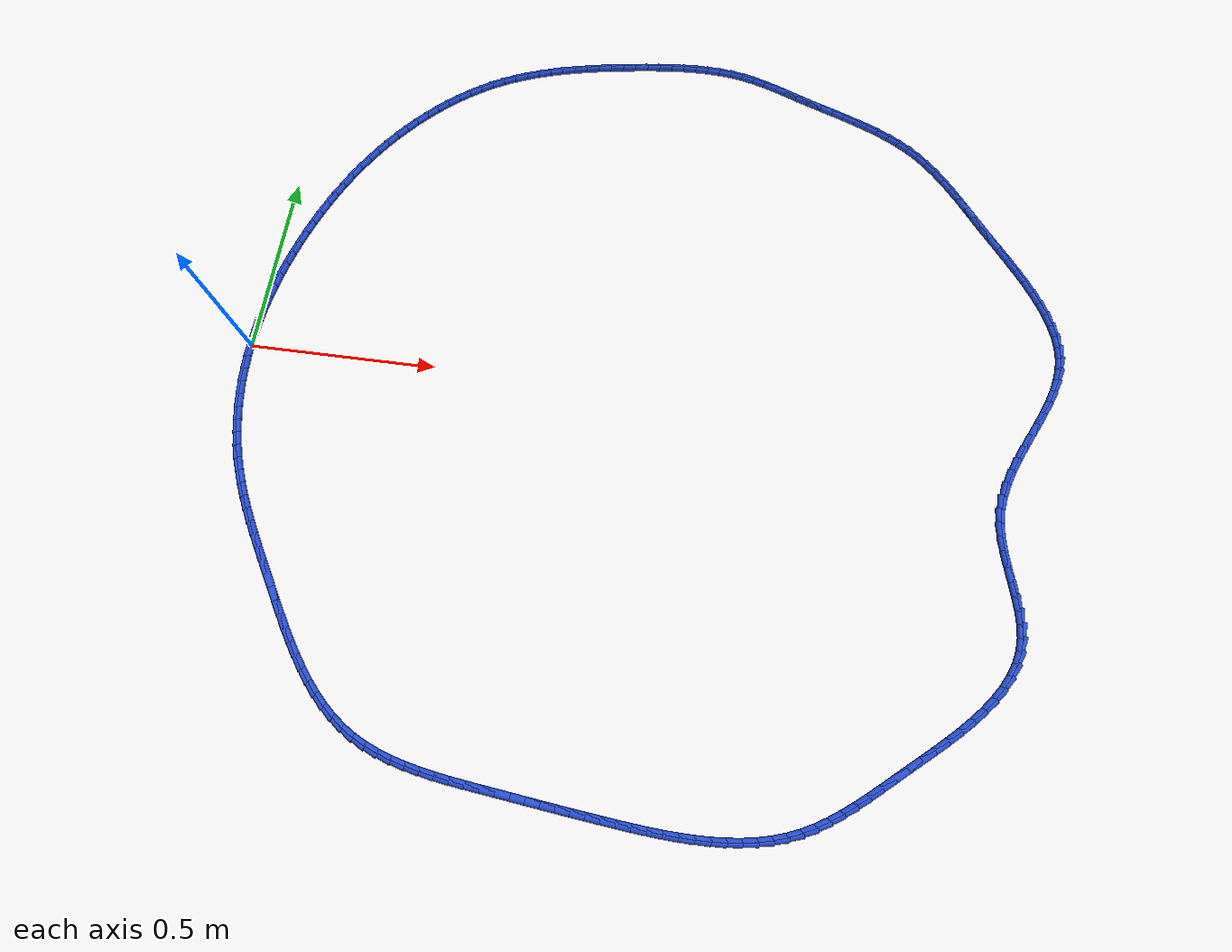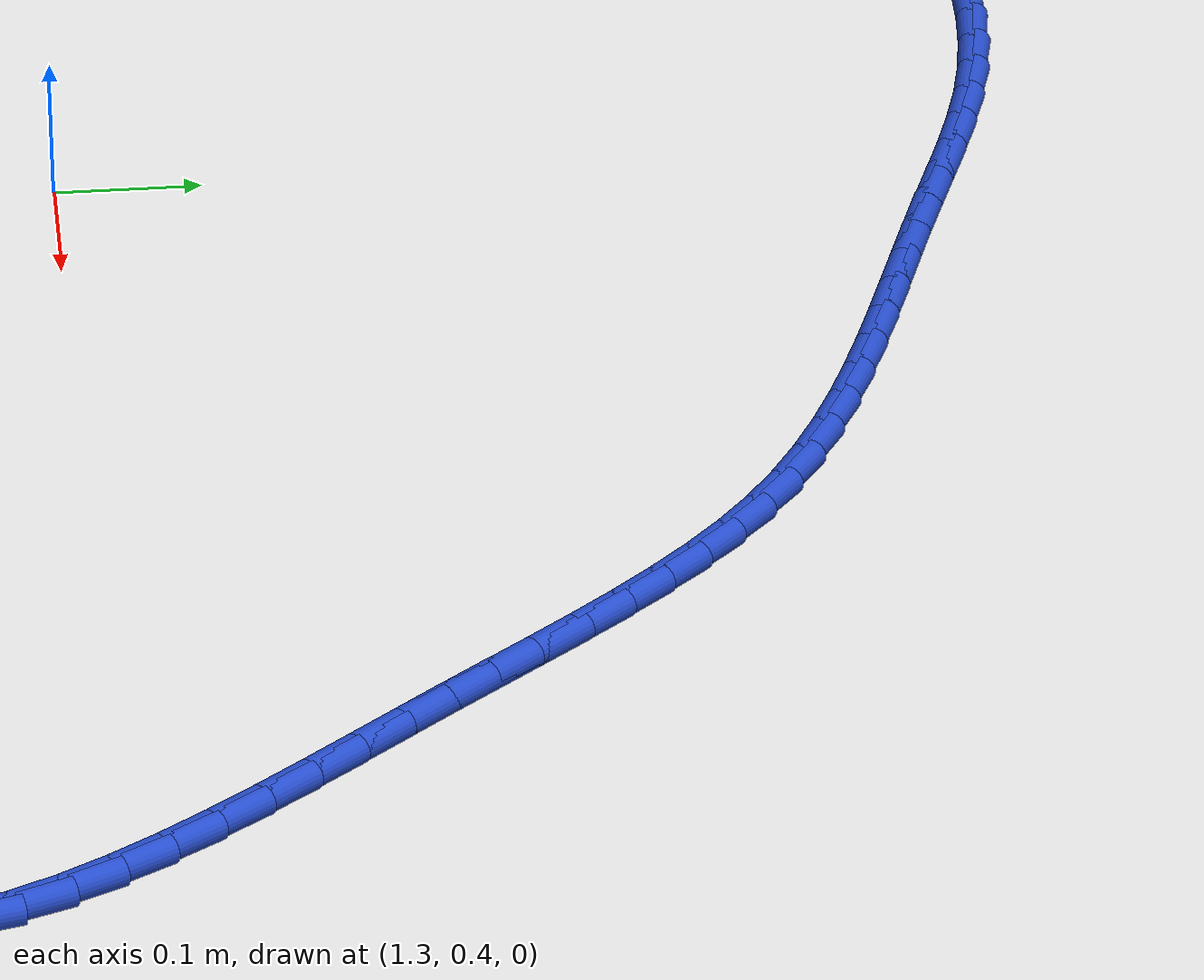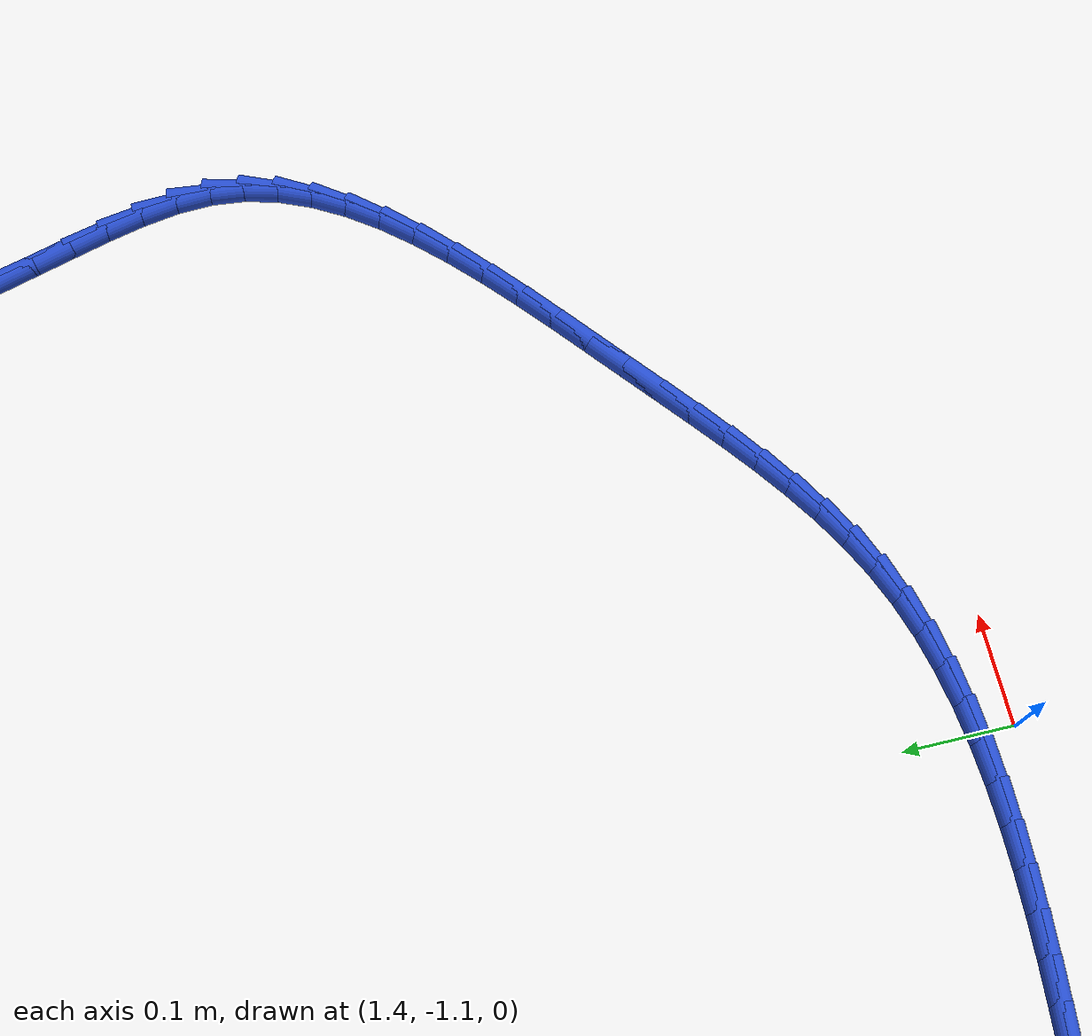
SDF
<sdf version="1.6">
 <world name="default">
  <light name="sun" type="directional">
   <pose>0 0 10 0 -0 0</pose>
   <diffuse>0.8 0.8 0.8 1</diffuse>
   <specular>0.2 0.2 0.2 1</specular>
   <attenuation>
    <range>1000</range>
    <constant>0.9</constant>
    <linear>0.01</linear>
    <quadratic>0.001</quadratic>
   </attenuation>
   <direction>-0.5 0.1 -0.9</direction>
  </light>
  <model name="ground_plane">
   <static>1</static>
   <link name="link">
    <collision name="collision">
     <geometry><plane><normal>0 0 1</normal><size>100 100</size></plane></geometry>
     <surface><friction><ode><mu>100</mu><mu2>50</mu2></ode></friction></surface>
    </collision>
    <visual name="visual">
     <cast_shadows>0</cast_shadows>
     <geometry><plane><normal>0 0 1</normal><size>100 100</size></plane></geometry>
     <material>
      <script><uri>file://media/materials/scripts/gazebo.material</uri><name>Gazebo/WhiteGlow</name></script>
     </material>
    </visual>
   </link>
  </model>
  <gravity>0 0 -9.8</gravity>
  <magnetic_field>6e-06 2.3e-05 -4.2e-05</magnetic_field>
  <atmosphere type="adiabatic"/>
  <physics name="default_physics" default="0" type="ode">
   <max_step_size>0.001</max_step_size>
   <real_time_factor>1</real_time_factor>
   <real_time_update_rate>1000</real_time_update_rate>
  </physics>
  <scene><ambient>0.4 0.4 0.4 1</ambient><background>0.7 0.7 0.7 1</background><shadows>1</shadows></scene>
  <spherical_coordinates>
   <surface_model>EARTH_WGS84</surface_model>
   <latitude_deg>0</latitude_deg>
   <longitude_deg>0</longitude_deg>
   <elevation>0</elevation>
   <heading_deg>0</heading_deg>
  </spherical_coordinates>
  <model name="line">
   <link name="link_0">
    <pose>-1.734723475976807e-18 -2.7755575615628914e-17 0.01 0 1.57 1.539559376418958</pose>
    <collision name="collision">
     <geometry><cylinder><radius>0.01</radius><length>0.08</length></cylinder></geometry>
    </collision>
    <visual name="visual">
     <material>
      <script><name>Gazebo/Blue</name><uri>file://media/materials/scripts/gazebo.material</uri></script>
     </material>
     <geometry><cylinder><radius>0.01</radius><length>0.08</length></cylinder></geometry>
    </visual>
   </link>
   <link name="link_1">
    <pose>0.0011212247587142708 0.035882505950260844 0.01 0 1.57 1.5037378693080572</pose>
    <collision name="collision">
     <geometry><cylinder><radius>0.01</radius><length>0.08</length></cylinder></geometry>
    </collision>
    <visual name="visual">
     <material>
      <script><name>Gazebo/Blue</name><uri>file://media/materials/scripts/gazebo.material</uri></script>
     </material>
     <geometry><cylinder><radius>0.01</radius><length>0.08</length></cylinder></geometry>
    </visual>
   </link>
   <link name="link_2">
    <pose>0.003522147219864937 0.07163224758675368 0.01 0 1.57 1.4692266333694144</pose>
    <collision name="collision">
     <geometry><cylinder><radius>0.01</radius><length>0.08</length></cylinder></geometry>
    </collision>
    <visual name="visual">
     <material>
      <script><name>Gazebo/Blue</name><uri>file://media/materials/scripts/gazebo.material</uri></script>
     </material>
     <geometry><cylinder><radius>0.01</radius><length>0.08</length></cylinder></geometry>
    </visual>
   </link>
   <link name="link_3">
    <pose>0.007150616097195604 0.10723324807625588 0.01 0 1.57 1.4360542948428303</pose>
    <collision name="collision">
     <geometry><cylinder><radius>0.01</radius><length>0.08</length></cylinder></geometry>
    </collision>
    <visual name="visual">
     <material>
      <script><name>Gazebo/Blue</name><uri>file://media/materials/scripts/gazebo.material</uri></script>
     </material>
     <geometry><cylinder><radius>0.01</radius><length>0.08</length></cylinder></geometry>
    </visual>
   </link>
   <link name="link_4">
    <pose>0.011954480104449869 0.14266953058554477 0.01 0 1.57 1.4042356273516454</pose>
    <collision name="collision">
     <geometry><cylinder><radius>0.01</radius><length>0.08</length></cylinder></geometry>
    </collision>
    <visual name="visual">
     <material>
      <script><name>Gazebo/Blue</name><uri>file://media/materials/scripts/gazebo.material</uri></script>
     </material>
     <geometry><cylinder><radius>0.01</radius><length>0.08</length></cylinder></geometry>
    </visual>
   </link>
   <link name="link_5">
    <pose>0.01788158795537134 0.17792511828139784 0.01 0 1.57 1.3737733214924168</pose>
    <collision name="collision">
     <geometry><cylinder><radius>0.01</radius><length>0.08</length></cylinder></geometry>
    </collision>
    <visual name="visual">
     <material>
      <script><name>Gazebo/Blue</name><uri>file://media/materials/scripts/gazebo.material</uri></script>
     </material>
     <geometry><cylinder><radius>0.01</radius><length>0.08</length></cylinder></geometry>
    </visual>
   </link>
   <link name="link_6">
    <pose>0.024879788363703616 0.21298403433059243 0.01 0 1.57 1.3446597969579952</pose>
    <collision name="collision">
     <geometry><cylinder><radius>0.01</radius><length>0.08</length></cylinder></geometry>
    </collision>
    <visual name="visual">
     <material>
      <script><name>Gazebo/Blue</name><uri>file://media/materials/scripts/gazebo.material</uri></script>
     </material>
     <geometry><cylinder><radius>0.01</radius><length>0.08</length></cylinder></geometry>
    </visual>
   </link>
   <link name="link_7">
    <pose>0.032896930043190276 0.24783030189990585 0.01 0 1.57 1.3168789789214657</pose>
    <collision name="collision">
     <geometry><cylinder><radius>0.01</radius><length>0.08</length></cylinder></geometry>
    </collision>
    <visual name="visual">
     <material>
      <script><name>Gazebo/Blue</name><uri>file://media/materials/scripts/gazebo.material</uri></script>
     </material>
     <geometry><cylinder><radius>0.01</radius><length>0.08</length></cylinder></geometry>
    </visual>
   </link>
   <link name="link_8">
    <pose>0.041880861707574955 0.2824479441561156 0.01 0 1.57 1.2904079813819704</pose>
    <collision name="collision">
     <geometry><cylinder><radius>0.01</radius><length>0.08</length></cylinder></geometry>
    </collision>
    <visual name="visual">
     <material>
      <script><name>Gazebo/Blue</name><uri>file://media/materials/scripts/gazebo.material</uri></script>
     </material>
     <geometry><cylinder><radius>0.01</radius><length>0.08</length></cylinder></geometry>
    </visual>
   </link>
   <link name="link_9">
    <pose>0.051779432070601226 0.31682098426599903 0.01 0 1.57 1.265045279841749</pose>
    <collision name="collision">
     <geometry><cylinder><radius>0.01</radius><length>0.08</length></cylinder></geometry>
    </collision>
    <visual name="visual">
     <material>
      <script><name>Gazebo/Blue</name><uri>file://media/materials/scripts/gazebo.material</uri></script>
     </material>
     <geometry><cylinder><radius>0.01</radius><length>0.08</length></cylinder></geometry>
    </visual>
   </link>
   <link name="link_10">
    <pose>0.06254649449430036 0.35093186554985445 0.01 0 1.57 1.2393477576886034</pose>
    <collision name="collision">
     <geometry><cylinder><radius>0.01</radius><length>0.08</length></cylinder></geometry>
    </collision>
    <visual name="visual">
     <material>
      <script><name>Gazebo/Blue</name><uri>file://media/materials/scripts/gazebo.material</uri></script>
     </material>
     <geometry><cylinder><radius>0.01</radius><length>0.08</length></cylinder></geometry>
    </visual>
   </link>
   <link name="link_11">
    <pose>0.07418486073779572 0.38475015018198017 0.01 0 1.57 1.2126019413082774</pose>
    <collision name="collision">
     <geometry><cylinder><radius>0.01</radius><length>0.08</length></cylinder></geometry>
    </collision>
    <visual name="visual">
     <material>
      <script><name>Gazebo/Blue</name><uri>file://media/materials/scripts/gazebo.material</uri></script>
     </material>
     <geometry><cylinder><radius>0.01</radius><length>0.08</length></cylinder></geometry>
    </visual>
   </link>
   <link name="link_12">
    <pose>0.08672121574540793 0.4182391192081603 0.01 0 1.57 1.1847837191620307</pose>
    <collision name="collision">
     <geometry><cylinder><radius>0.01</radius><length>0.08</length></cylinder></geometry>
    </collision>
    <visual name="visual">
     <material>
      <script><name>Gazebo/Blue</name><uri>file://media/materials/scripts/gazebo.material</uri></script>
     </material>
     <geometry><cylinder><radius>0.01</radius><length>0.08</length></cylinder></geometry>
    </visual>
   </link>
   <link name="link_13">
    <pose>0.10018240520271063 0.45136201138252496 0.01 0 1.57 1.15587867154603</pose>
    <collision name="collision">
     <geometry><cylinder><radius>0.01</radius><length>0.08</length></cylinder></geometry>
    </collision>
    <visual name="visual">
     <material>
      <script><name>Gazebo/Blue</name><uri>file://media/materials/scripts/gazebo.material</uri></script>
     </material>
     <geometry><cylinder><radius>0.01</radius><length>0.08</length></cylinder></geometry>
    </visual>
   </link>
   <link name="link_14">
    <pose>0.11459527479527756 0.48408206545920524 0.01 0 1.57 1.1258784939448632</pose>
    <collision name="collision">
     <geometry><cylinder><radius>0.01</radius><length>0.08</length></cylinder></geometry>
    </collision>
    <visual name="visual">
     <material>
      <script><name>Gazebo/Blue</name><uri>file://media/materials/scripts/gazebo.material</uri></script>
     </material>
     <geometry><cylinder><radius>0.01</radius><length>0.08</length></cylinder></geometry>
    </visual>
   </link>
   <link name="link_15">
    <pose>0.12998667020868243 0.5163625201923318 0.01 0 1.57 1.094782118080417</pose>
    <collision name="collision">
     <geometry><cylinder><radius>0.01</radius><length>0.08</length></cylinder></geometry>
    </collision>
    <visual name="visual">
     <material>
      <script><name>Gazebo/Blue</name><uri>file://media/materials/scripts/gazebo.material</uri></script>
     </material>
     <geometry><cylinder><radius>0.01</radius><length>0.08</length></cylinder></geometry>
    </visual>
   </link>
   <link name="link_16">
    <pose>0.14638343712849897 0.5481666143360352 0.01 0 1.57 1.062596859016838</pose>
    <collision name="collision">
     <geometry><cylinder><radius>0.01</radius><length>0.08</length></cylinder></geometry>
    </collision>
    <visual name="visual">
     <material>
      <script><name>Gazebo/Blue</name><uri>file://media/materials/scripts/gazebo.material</uri></script>
     </material>
     <geometry><cylinder><radius>0.01</radius><length>0.08</length></cylinder></geometry>
    </visual>
   </link>
   <link name="link_17">
    <pose>0.16381242124030085 0.5794575866444461 0.01 0 1.57 1.0293395476816007</pose>
    <collision name="collision">
     <geometry><cylinder><radius>0.01</radius><length>0.08</length></cylinder></geometry>
    </collision>
    <visual name="visual">
     <material>
      <script><name>Gazebo/Blue</name><uri>file://media/materials/scripts/gazebo.material</uri></script>
     </material>
     <geometry><cylinder><radius>0.01</radius><length>0.08</length></cylinder></geometry>
    </visual>
   </link>
   <link name="link_18">
    <pose>0.18230046822966178 0.6101986758716953 0.01 0 1.57 0.9950375978235502</pose>
    <collision name="collision">
     <geometry><cylinder><radius>0.01</radius><length>0.08</length></cylinder></geometry>
    </collision>
    <visual name="visual">
     <material>
      <script><name>Gazebo/Blue</name><uri>file://media/materials/scripts/gazebo.material</uri></script>
     </material>
     <geometry><cylinder><radius>0.01</radius><length>0.08</length></cylinder></geometry>
    </visual>
   </link>
   <link name="link_19">
    <pose>0.20187442378215542 0.6403531207719132 0.01 0 1.57 0.9597320672533927</pose>
    <collision name="collision">
     <geometry><cylinder><radius>0.01</radius><length>0.08</length></cylinder></geometry>
    </collision>
    <visual name="visual">
     <material>
      <script><name>Gazebo/Blue</name><uri>file://media/materials/scripts/gazebo.material</uri></script>
     </material>
     <geometry><cylinder><radius>0.01</radius><length>0.08</length></cylinder></geometry>
    </visual>
   </link>
   <link name="link_20">
    <pose>0.22256081399075195 0.669883837109027 0.01 0 1.57 0.9235845779372743</pose>
    <collision name="collision">
     <geometry><cylinder><radius>0.01</radius><length>0.08</length></cylinder></geometry>
    </collision>
    <visual name="visual">
     <material>
      <script><name>Gazebo/Blue</name><uri>file://media/materials/scripts/gazebo.material</uri></script>
     </material>
     <geometry><cylinder><radius>0.01</radius><length>0.08</length></cylinder></geometry>
    </visual>
   </link>
   <link name="link_21">
    <pose>0.244364690070802 0.6987320374691689 0.01 0 1.57 0.8866937454770051</pose>
    <collision name="collision">
     <geometry><cylinder><radius>0.01</radius><length>0.08</length></cylinder></geometry>
    </collision>
    <visual name="visual">
     <material>
      <script><name>Gazebo/Blue</name><uri>file://media/materials/scripts/gazebo.material</uri></script>
     </material>
     <geometry><cylinder><radius>0.01</radius><length>0.08</length></cylinder></geometry>
    </visual>
   </link>
   <link name="link_22">
    <pose>0.26725642309423836 0.7268038856092353 0.01 0 1.57 0.8488897395789047</pose>
    <collision name="collision">
     <geometry><cylinder><radius>0.01</radius><length>0.08</length></cylinder></geometry>
    </collision>
    <visual name="visual">
     <material>
      <script><name>Gazebo/Blue</name><uri>file://media/materials/scripts/gazebo.material</uri></script>
     </material>
     <geometry><cylinder><radius>0.01</radius><length>0.08</length></cylinder></geometry>
    </visual>
   </link>
   <link name="link_23">
    <pose>0.2912032317909708 0.7540023594314411 0.01 0 1.57 0.8099839046036821</pose>
    <collision name="collision">
     <geometry><cylinder><radius>0.01</radius><length>0.08</length></cylinder></geometry>
    </collision>
    <visual name="visual">
     <material>
      <script><name>Gazebo/Blue</name><uri>file://media/materials/scripts/gazebo.material</uri></script>
     </material>
     <geometry><cylinder><radius>0.01</radius><length>0.08</length></cylinder></geometry>
    </visual>
   </link>
   <link name="link_24">
    <pose>0.31617233489090935 0.7802304368380025 0.01 0 1.57 0.7697897155766197</pose>
    <collision name="collision">
     <geometry><cylinder><radius>0.01</radius><length>0.08</length></cylinder></geometry>
    </collision>
    <visual name="visual">
     <material>
      <script><name>Gazebo/Blue</name><uri>file://media/materials/scripts/gazebo.material</uri></script>
     </material>
     <geometry><cylinder><radius>0.01</radius><length>0.08</length></cylinder></geometry>
    </visual>
   </link>
   <link name="link_25">
    <pose>0.34213095112396363 0.8053910957311339 0.01 0 1.57 0.7281236111264333</pose>
    <collision name="collision">
     <geometry><cylinder><radius>0.01</radius><length>0.08</length></cylinder></geometry>
    </collision>
    <visual name="visual">
     <material>
      <script><name>Gazebo/Blue</name><uri>file://media/materials/scripts/gazebo.material</uri></script>
     </material>
     <geometry><cylinder><radius>0.01</radius><length>0.08</length></cylinder></geometry>
    </visual>
   </link>
   <link name="link_26">
    <pose>0.36904629922004384 0.8293873140130511 0.01 0 1.57 0.6848067717463668</pose>
    <collision name="collision">
     <geometry><cylinder><radius>0.01</radius><length>0.08</length></cylinder></geometry>
    </collision>
    <visual name="visual">
     <material>
      <script><name>Gazebo/Blue</name><uri>file://media/materials/scripts/gazebo.material</uri></script>
     </material>
     <geometry><cylinder><radius>0.01</radius><length>0.08</length></cylinder></geometry>
    </visual>
   </link>
   <link name="link_27">
    <pose>0.39688559790905975 0.8521220695859691 0.01 0 1.57 0.639668017552806</pose>
    <collision name="collision">
     <geometry><cylinder><radius>0.01</radius><length>0.08</length></cylinder></geometry>
    </collision>
    <visual name="visual">
     <material>
      <script><name>Gazebo/Blue</name><uri>file://media/materials/scripts/gazebo.material</uri></script>
     </material>
     <geometry><cylinder><radius>0.01</radius><length>0.08</length></cylinder></geometry>
    </visual>
   </link>
   <link name="link_28">
    <pose>0.4256160659209209 0.8734983403521029 0.01 0 1.57 0.592548005027577</pose>
    <collision name="collision">
     <geometry><cylinder><radius>0.01</radius><length>0.08</length></cylinder></geometry>
    </collision>
    <visual name="visual">
     <material>
      <script><name>Gazebo/Blue</name><uri>file://media/materials/scripts/gazebo.material</uri></script>
     </material>
     <geometry><cylinder><radius>0.01</radius><length>0.08</length></cylinder></geometry>
    </visual>
   </link>
   <link name="link_29">
    <pose>0.45520492198553775 0.8934191042136685 0.01 0 1.57 0.543304878671618</pose>
    <collision name="collision">
     <geometry><cylinder><radius>0.01</radius><length>0.08</length></cylinder></geometry>
    </collision>
    <visual name="visual">
     <material>
      <script><name>Gazebo/Blue</name><uri>file://media/materials/scripts/gazebo.material</uri></script>
     </material>
     <geometry><cylinder><radius>0.01</radius><length>0.08</length></cylinder></geometry>
    </visual>
   </link>
   <link name="link_30">
    <pose>0.48561938483281963 0.9117873390728806 0.01 0 1.57 0.49193047307201054</pose>
    <collision name="collision">
     <geometry><cylinder><radius>0.01</radius><length>0.08</length></cylinder></geometry>
    </collision>
    <visual name="visual">
     <material>
      <script><name>Gazebo/Blue</name><uri>file://media/materials/scripts/gazebo.material</uri></script>
     </material>
     <geometry><cylinder><radius>0.01</radius><length>0.08</length></cylinder></geometry>
    </visual>
   </link>
   <link name="link_31">
    <pose>0.5168261524215624 0.928510122227202 0.01 0 1.57 0.4411245502686114</pose>
    <collision name="collision">
     <geometry><cylinder><radius>0.01</radius><length>0.08</length></cylinder></geometry>
    </collision>
    <visual name="visual">
     <material>
      <script><name>Gazebo/Blue</name><uri>file://media/materials/scripts/gazebo.material</uri></script>
     </material>
     <geometry><cylinder><radius>0.01</radius><length>0.08</length></cylinder></geometry>
    </visual>
   </link>
   <link name="link_32">
    <pose>0.5487789323213479 0.9435967884501849 0.01 0 1.57 0.39393522412077314</pose>
    <collision name="collision">
     <geometry><cylinder><radius>0.01</radius><length>0.08</length></cylinder></geometry>
    </collision>
    <visual name="visual">
     <material>
      <script><name>Gazebo/Blue</name><uri>file://media/materials/scripts/gazebo.material</uri></script>
     </material>
     <geometry><cylinder><radius>0.01</radius><length>0.08</length></cylinder></geometry>
    </visual>
   </link>
   <link name="link_33">
    <pose>0.5814178529054369 0.9571635649510432 0.01 0 1.57 0.35067977942888773</pose>
    <collision name="collision">
     <geometry><cylinder><radius>0.01</radius><length>0.08</length></cylinder></geometry>
    </collision>
    <visual name="visual">
     <material>
      <script><name>Gazebo/Blue</name><uri>file://media/materials/scripts/gazebo.material</uri></script>
     </material>
     <geometry><cylinder><radius>0.01</radius><length>0.08</length></cylinder></geometry>
    </visual>
   </link>
   <link name="link_34">
    <pose>0.6146824039420071 0.9693317058972302 0.01 0 1.57 0.3114519781689955</pose>
    <collision name="collision">
     <geometry><cylinder><radius>0.01</radius><length>0.08</length></cylinder></geometry>
    </collision>
    <visual name="visual">
     <material>
      <script><name>Gazebo/Blue</name><uri>file://media/materials/scripts/gazebo.material</uri></script>
     </material>
     <geometry><cylinder><radius>0.01</radius><length>0.08</length></cylinder></geometry>
    </visual>
   </link>
   <link name="link_35">
    <pose>0.6485120751992353 0.9802224654561976 0.01 0 1.57 0.2762745754789621</pose>
    <collision name="collision">
     <geometry><cylinder><radius>0.01</radius><length>0.08</length></cylinder></geometry>
    </collision>
    <visual name="visual">
     <material>
      <script><name>Gazebo/Blue</name><uri>file://media/materials/scripts/gazebo.material</uri></script>
     </material>
     <geometry><cylinder><radius>0.01</radius><length>0.08</length></cylinder></geometry>
    </visual>
   </link>
   <link name="link_36">
    <pose>0.6828463564452986 0.9899570977953981 0.01 0 1.57 0.24511840797166237</pose>
    <collision name="collision">
     <geometry><cylinder><radius>0.01</radius><length>0.08</length></cylinder></geometry>
    </collision>
    <visual name="visual">
     <material>
      <script><name>Gazebo/Blue</name><uri>file://media/materials/scripts/gazebo.material</uri></script>
     </material>
     <geometry><cylinder><radius>0.01</radius><length>0.08</length></cylinder></geometry>
    </visual>
   </link>
   <link name="link_37">
    <pose>0.7176247374483741 0.998656857082284 0.01 0 1.57 0.21791998529759293</pose>
    <collision name="collision">
     <geometry><cylinder><radius>0.01</radius><length>0.08</length></cylinder></geometry>
    </collision>
    <visual name="visual">
     <material>
      <script><name>Gazebo/Blue</name><uri>file://media/materials/scripts/gazebo.material</uri></script>
     </material>
     <geometry><cylinder><radius>0.01</radius><length>0.08</length></cylinder></geometry>
    </visual>
   </link>
   <link name="link_38">
    <pose>0.7527867079766393 1.0064429974843079 0.01 0 1.57 0.1945966617900141</pose>
    <collision name="collision">
     <geometry><cylinder><radius>0.01</radius><length>0.08</length></cylinder></geometry>
    </collision>
    <visual name="visual">
     <material>
      <script><name>Gazebo/Blue</name><uri>file://media/materials/scripts/gazebo.material</uri></script>
     </material>
     <geometry><cylinder><radius>0.01</radius><length>0.08</length></cylinder></geometry>
    </visual>
   </link>
   <link name="link_39">
    <pose>0.7882717577982709 1.0134367731689218 0.01 0 1.57 0.17505908160923872</pose>
    <collision name="collision">
     <geometry><cylinder><radius>0.01</radius><length>0.08</length></cylinder></geometry>
    </collision>
    <visual name="visual">
     <material>
      <script><name>Gazebo/Blue</name><uri>file://media/materials/scripts/gazebo.material</uri></script>
     </material>
     <geometry><cylinder><radius>0.01</radius><length>0.08</length></cylinder></geometry>
    </visual>
   </link>
   <link name="link_40">
    <pose>0.8240193766814464 1.0197594383035784 0.01 0 1.57 0.15922099133254172</pose>
    <collision name="collision">
     <geometry><cylinder><radius>0.01</radius><length>0.08</length></cylinder></geometry>
    </collision>
    <visual name="visual">
     <material>
      <script><name>Gazebo/Blue</name><uri>file://media/materials/scripts/gazebo.material</uri></script>
     </material>
     <geometry><cylinder><radius>0.01</radius><length>0.08</length></cylinder></geometry>
    </visual>
   </link>
   <link name="link_41">
    <pose>0.859969054394343 1.0255322470557304 0.01 0 1.57 0.14700672867535905</pose>
    <collision name="collision">
     <geometry><cylinder><radius>0.01</radius><length>0.08</length></cylinder></geometry>
    </collision>
    <visual name="visual">
     <material>
      <script><name>Gazebo/Blue</name><uri>file://media/materials/scripts/gazebo.material</uri></script>
     </material>
     <geometry><cylinder><radius>0.01</radius><length>0.08</length></cylinder></geometry>
    </visual>
   </link>
   <link name="link_42">
    <pose>0.8960602807051377 1.0308764535928299 0.01 0 1.57 0.1368987091131055</pose>
    <collision name="collision">
     <geometry><cylinder><radius>0.01</radius><length>0.08</length></cylinder></geometry>
    </collision>
    <visual name="visual">
     <material>
      <script><name>Gazebo/Blue</name><uri>file://media/materials/scripts/gazebo.material</uri></script>
     </material>
     <geometry><cylinder><radius>0.01</radius><length>0.08</length></cylinder></geometry>
    </visual>
   </link>
   <link name="link_43">
    <pose>0.9322327910663226 1.0358595926263783 0.01 0 1.57 0.12258911371297612</pose>
    <collision name="collision">
     <geometry><cylinder><radius>0.01</radius><length>0.08</length></cylinder></geometry>
    </collision>
    <visual name="visual">
     <material>
      <script><name>Gazebo/Blue</name><uri>file://media/materials/scripts/gazebo.material</uri></script>
     </material>
     <geometry><cylinder><radius>0.01</radius><length>0.08</length></cylinder></geometry>
    </visual>
   </link>
   <link name="link_44">
    <pose>0.9684273736661217 1.0403190157129738 0.01 0 1.57 0.10228699814109113</pose>
    <collision name="collision">
     <geometry><cylinder><radius>0.01</radius><length>0.08</length></cylinder></geometry>
    </collision>
    <visual name="visual">
     <material>
      <script><name>Gazebo/Blue</name><uri>file://media/materials/scripts/gazebo.material</uri></script>
     </material>
     <geometry><cylinder><radius>0.01</radius><length>0.08</length></cylinder></geometry>
    </visual>
   </link>
   <link name="link_45">
    <pose>1.00458509860503 1.0440304336247375 0.01 0 1.57 0.07581049561710813</pose>
    <collision name="collision">
     <geometry><cylinder><radius>0.01</radius><length>0.08</length></cylinder></geometry>
    </collision>
    <visual name="visual">
     <material>
      <script><name>Gazebo/Blue</name><uri>file://media/materials/scripts/gazebo.material</uri></script>
     </material>
     <geometry><cylinder><radius>0.01</radius><length>0.08</length></cylinder></geometry>
    </visual>
   </link>
   <link name="link_46">
    <pose>1.04064703598672 1.0467695564396235 0.01 0 1.57 0.04293258970237798</pose>
    <collision name="collision">
     <geometry><cylinder><radius>0.01</radius><length>0.08</length></cylinder></geometry>
    </collision>
    <visual name="visual">
     <material>
      <script><name>Gazebo/Blue</name><uri>file://media/materials/scripts/gazebo.material</uri></script>
     </material>
     <geometry><cylinder><radius>0.01</radius><length>0.08</length></cylinder></geometry>
    </visual>
   </link>
   <link name="link_47">
    <pose>1.0765542559148609 1.0483120942355846 0.01 0 1.57 0.0034085235811668804</pose>
    <collision name="collision">
     <geometry><cylinder><radius>0.01</radius><length>0.08</length></cylinder></geometry>
    </collision>
    <visual name="visual">
     <material>
      <script><name>Gazebo/Blue</name><uri>file://media/materials/scripts/gazebo.material</uri></script>
     </material>
     <geometry><cylinder><radius>0.01</radius><length>0.08</length></cylinder></geometry>
    </visual>
   </link>
   <link name="link_48">
    <pose>1.1122478284931245 1.048433757090575 0.01 0 1.57 -0.04298477662256288</pose>
    <collision name="collision">
     <geometry><cylinder><radius>0.01</radius><length>0.08</length></cylinder></geometry>
    </collision>
    <visual name="visual">
     <material>
      <script><name>Gazebo/Blue</name><uri>file://media/materials/scripts/gazebo.material</uri></script>
     </material>
     <geometry><cylinder><radius>0.01</radius><length>0.08</length></cylinder></geometry>
    </visual>
   </link>
   <link name="link_49">
    <pose>1.147668823825181 1.0469102550825486 0.01 0 1.57 -0.09639471534827782</pose>
    <collision name="collision">
     <geometry><cylinder><radius>0.01</radius><length>0.08</length></cylinder></geometry>
    </collision>
    <visual name="visual">
     <material>
      <script><name>Gazebo/Blue</name><uri>file://media/materials/scripts/gazebo.material</uri></script>
     </material>
     <geometry><cylinder><radius>0.01</radius><length>0.08</length></cylinder></geometry>
    </visual>
   </link>
   <link name="link_50">
    <pose>1.1827583120147025 1.0435172982894587 0.01 0 1.57 -0.1568241142151317</pose>
    <collision name="collision">
     <geometry><cylinder><radius>0.01</radius><length>0.08</length></cylinder></geometry>
    </collision>
    <visual name="visual">
     <material>
      <script><name>Gazebo/Blue</name><uri>file://media/materials/scripts/gazebo.material</uri></script>
     </material>
     <geometry><cylinder><radius>0.01</radius><length>0.08</length></cylinder></geometry>
    </visual>
   </link>
   <link name="link_51">
    <pose>1.2174573631653587 1.0380305967892591 0.01 0 1.57 -0.22300901044112229</pose>
    <collision name="collision">
     <geometry><cylinder><radius>0.01</radius><length>0.08</length></cylinder></geometry>
    </collision>
    <visual name="visual">
     <material>
      <script><name>Gazebo/Blue</name><uri>file://media/materials/scripts/gazebo.material</uri></script>
     </material>
     <geometry><cylinder><radius>0.01</radius><length>0.08</length></cylinder></geometry>
    </visual>
   </link>
   <link name="link_52">
    <pose>1.2517173360250047 1.0302610846378832 0.01 0 1.57 -0.2815972012523768</pose>
    <collision name="collision">
     <geometry><cylinder><radius>0.01</radius><length>0.08</length></cylinder></geometry>
    </collision>
    <visual name="visual">
     <material>
      <script><name>Gazebo/Blue</name><uri>file://media/materials/scripts/gazebo.material</uri></script>
     </material>
     <geometry><cylinder><radius>0.01</radius><length>0.08</length></cylinder></geometry>
    </visual>
   </link>
   <link name="link_53">
    <pose>1.2856166080447815 1.0204545543553882 0.01 0 1.57 -0.3236313328263289</pose>
    <collision name="collision">
     <geometry><cylinder><radius>0.01</radius><length>0.08</length></cylinder></geometry>
    </collision>
    <visual name="visual">
     <material>
      <script><name>Gazebo/Blue</name><uri>file://media/materials/scripts/gazebo.material</uri></script>
     </material>
     <geometry><cylinder><radius>0.01</radius><length>0.08</length></cylinder></geometry>
    </visual>
   </link>
   <link name="link_54">
    <pose>1.319319167430689 1.009149893576221 0.01 0 1.57 -0.349145117064477</pose>
    <collision name="collision">
     <geometry><cylinder><radius>0.01</radius><length>0.08</length></cylinder></geometry>
    </collision>
    <visual name="visual">
     <material>
      <script><name>Gazebo/Blue</name><uri>file://media/materials/scripts/gazebo.material</uri></script>
     </material>
     <geometry><cylinder><radius>0.01</radius><length>0.08</length></cylinder></geometry>
    </visual>
   </link>
   <link name="link_55">
    <pose>1.3529906032230097 0.9968914705161926 0.01 0 1.57 -0.35852697906041325</pose>
    <collision name="collision">
     <geometry><cylinder><radius>0.01</radius><length>0.08</length></cylinder></geometry>
    </collision>
    <visual name="visual">
     <material>
      <script><name>Gazebo/Blue</name><uri>file://media/materials/scripts/gazebo.material</uri></script>
     </material>
     <geometry><cylinder><radius>0.01</radius><length>0.08</length></cylinder></geometry>
    </visual>
   </link>
   <link name="link_56">
    <pose>1.3867965044620254 0.9842236533911132 0.01 0 1.57 -0.35238301375654507</pose>
    <collision name="collision">
     <geometry><cylinder><radius>0.01</radius><length>0.08</length></cylinder></geometry>
    </collision>
    <visual name="visual">
     <material>
      <script><name>Gazebo/Blue</name><uri>file://media/materials/scripts/gazebo.material</uri></script>
     </material>
     <geometry><cylinder><radius>0.01</radius><length>0.08</length></cylinder></geometry>
    </visual>
   </link>
   <link name="link_57">
    <pose>1.4208988359415666 0.9716831555846003 0.01 0 1.57 -0.3407236540394247</pose>
    <collision name="collision">
     <geometry><cylinder><radius>0.01</radius><length>0.08</length></cylinder></geometry>
    </collision>
    <visual name="visual">
     <material>
      <script><name>Gazebo/Blue</name><uri>file://media/materials/scripts/gazebo.material</uri></script>
     </material>
     <geometry><cylinder><radius>0.01</radius><length>0.08</length></cylinder></geometry>
    </visual>
   </link>
   <link name="link_58">
    <pose>1.4553066902074827 0.9594838064214619 0.01 0 1.57 -0.3366292014043472</pose>
    <collision name="collision">
     <geometry><cylinder><radius>0.01</radius><length>0.08</length></cylinder></geometry>
    </collision>
    <visual name="visual">
     <material>
      <script><name>Gazebo/Blue</name><uri>file://media/materials/scripts/gazebo.material</uri></script>
     </material>
     <geometry><cylinder><radius>0.01</radius><length>0.08</length></cylinder></geometry>
    </visual>
   </link>
   <link name="link_59">
    <pose>1.4898233508427476 0.9474047426374187 0.01 0 1.57 -0.3409473030265532</pose>
    <collision name="collision">
     <geometry><cylinder><radius>0.01</radius><length>0.08</length></cylinder></geometry>
    </collision>
    <visual name="visual">
     <material>
      <script><name>Gazebo/Blue</name><uri>file://media/materials/scripts/gazebo.material</uri></script>
     </material>
     <geometry><cylinder><radius>0.01</radius><length>0.08</length></cylinder></geometry>
    </visual>
   </link>
   <link name="link_60">
    <pose>1.52423759553224 0.9351944628156442 0.01 0 1.57 -0.3537548652159454</pose>
    <collision name="collision">
     <geometry><cylinder><radius>0.01</radius><length>0.08</length></cylinder></geometry>
    </collision>
    <visual name="visual">
     <material>
      <script><name>Gazebo/Blue</name><uri>file://media/materials/scripts/gazebo.material</uri></script>
     </material>
     <geometry><cylinder><radius>0.01</radius><length>0.08</length></cylinder></geometry>
    </visual>
   </link>
   <link name="link_61">
    <pose>1.5583382019608372 0.9226014655393117 0.01 0 1.57 -0.37528132073103376</pose>
    <collision name="collision">
     <geometry><cylinder><radius>0.01</radius><length>0.08</length></cylinder></geometry>
    </collision>
    <visual name="visual">
     <material>
      <script><name>Gazebo/Blue</name><uri>file://media/materials/scripts/gazebo.material</uri></script>
     </material>
     <geometry><cylinder><radius>0.01</radius><length>0.08</length></cylinder></geometry>
    </visual>
   </link>
   <link name="link_62">
    <pose>1.591913947813417 0.9093742493915942 0.01 0 1.57 -0.405889397109304</pose>
    <collision name="collision">
     <geometry><cylinder><radius>0.01</radius><length>0.08</length></cylinder></geometry>
    </collision>
    <visual name="visual">
     <material>
      <script><name>Gazebo/Blue</name><uri>file://media/materials/scripts/gazebo.material</uri></script>
     </material>
     <geometry><cylinder><radius>0.01</radius><length>0.08</length></cylinder></geometry>
    </visual>
   </link>
   <link name="link_63">
    <pose>1.6247536107748575 0.8952613129556656 0.01 0 1.57 -0.44603642686886424</pose>
    <collision name="collision">
     <geometry><cylinder><radius>0.01</radius><length>0.08</length></cylinder></geometry>
    </collision>
    <visual name="visual">
     <material>
      <script><name>Gazebo/Blue</name><uri>file://media/materials/scripts/gazebo.material</uri></script>
     </material>
     <geometry><cylinder><radius>0.01</radius><length>0.08</length></cylinder></geometry>
    </visual>
   </link>
   <link name="link_64">
    <pose>1.6566459685300368 0.8800111548146987 0.01 0 1.57 -0.4962061280114834</pose>
    <collision name="collision">
     <geometry><cylinder><radius>0.01</radius><length>0.08</length></cylinder></geometry>
    </collision>
    <visual name="visual">
     <material>
      <script><name>Gazebo/Blue</name><uri>file://media/materials/scripts/gazebo.material</uri></script>
     </material>
     <geometry><cylinder><radius>0.01</radius><length>0.08</length></cylinder></geometry>
    </visual>
   </link>
   <link name="link_65">
    <pose>1.6873797987638326 0.863372273551867 0.01 0 1.57 -0.5567987017231645</pose>
    <collision name="collision">
     <geometry><cylinder><radius>0.01</radius><length>0.08</length></cylinder></geometry>
    </collision>
    <visual name="visual">
     <material>
      <script><name>Gazebo/Blue</name><uri>file://media/materials/scripts/gazebo.material</uri></script>
     </material>
     <geometry><cylinder><radius>0.01</radius><length>0.08</length></cylinder></geometry>
    </visual>
   </link>
   <link name="link_66">
    <pose>1.7167438791611238 0.8450931677503447 0.01 0 1.57 -0.627661396016519</pose>
    <collision name="collision">
     <geometry><cylinder><radius>0.01</radius><length>0.08</length></cylinder></geometry>
    </collision>
    <visual name="visual">
     <material>
      <script><name>Gazebo/Blue</name><uri>file://media/materials/scripts/gazebo.material</uri></script>
     </material>
     <geometry><cylinder><radius>0.01</radius><length>0.08</length></cylinder></geometry>
    </visual>
   </link>
   <link name="link_67">
    <pose>1.7445349018754455 0.8249296970740361 0.01 0 1.57 -0.6996685758827992</pose>
    <collision name="collision">
     <geometry><cylinder><radius>0.01</radius><length>0.08</length></cylinder></geometry>
    </collision>
    <visual name="visual">
     <material>
      <script><name>Gazebo/Blue</name><uri>file://media/materials/scripts/gazebo.material</uri></script>
     </material>
     <geometry><cylinder><radius>0.01</radius><length>0.08</length></cylinder></geometry>
    </visual>
   </link>
   <link name="link_68">
    <pose>1.7707724209945344 0.802845000381508 0.01 0 1.57 -0.7620269153508226</pose>
    <collision name="collision">
     <geometry><cylinder><radius>0.01</radius><length>0.08</length></cylinder></geometry>
    </collision>
    <visual name="visual">
     <material>
      <script><name>Gazebo/Blue</name><uri>file://media/materials/scripts/gazebo.material</uri></script>
     </material>
     <geometry><cylinder><radius>0.01</radius><length>0.08</length></cylinder></geometry>
    </visual>
   </link>
   <link name="link_69">
    <pose>1.7957242138897613 0.7790330837833489 0.01 0 1.57 -0.8135195737571825</pose>
    <collision name="collision">
     <geometry><cylinder><radius>0.01</radius><length>0.08</length></cylinder></geometry>
    </collision>
    <visual name="visual">
     <material>
      <script><name>Gazebo/Blue</name><uri>file://media/materials/scripts/gazebo.material</uri></script>
     </material>
     <geometry><cylinder><radius>0.01</radius><length>0.08</length></cylinder></geometry>
    </visual>
   </link>
   <link name="link_70">
    <pose>1.8196710631477928 0.7537000492671835 0.01 0 1.57 -0.8539752694724836</pose>
    <collision name="collision">
     <geometry><cylinder><radius>0.01</radius><length>0.08</length></cylinder></geometry>
    </collision>
    <visual name="visual">
     <material>
      <script><name>Gazebo/Blue</name><uri>file://media/materials/scripts/gazebo.material</uri></script>
     </material>
     <geometry><cylinder><radius>0.01</radius><length>0.08</length></cylinder></geometry>
    </visual>
   </link>
   <link name="link_71">
    <pose>1.8428937513552923 0.7270519988206351 0.01 0 1.57 -0.8835781484796419</pose>
    <collision name="collision">
     <geometry><cylinder><radius>0.01</radius><length>0.08</length></cylinder></geometry>
    </collision>
    <visual name="visual">
     <material>
      <script><name>Gazebo/Blue</name><uri>file://media/materials/scripts/gazebo.material</uri></script>
     </material>
     <geometry><cylinder><radius>0.01</radius><length>0.08</length></cylinder></geometry>
    </visual>
   </link>
   <link name="link_72">
    <pose>1.8656730610989243 0.6992950344313279 0.01 0 1.57 -0.9027095380230736</pose>
    <collision name="collision">
     <geometry><cylinder><radius>0.01</radius><length>0.08</length></cylinder></geometry>
    </collision>
    <visual name="visual">
     <material>
      <script><name>Gazebo/Blue</name><uri>file://media/materials/scripts/gazebo.material</uri></script>
     </material>
     <geometry><cylinder><radius>0.01</radius><length>0.08</length></cylinder></geometry>
    </visual>
   </link>
   <link name="link_73">
    <pose>1.8882897749653529 0.6706352580868865 0.01 0 1.57 -0.9118348684600265</pose>
    <collision name="collision">
     <geometry><cylinder><radius>0.01</radius><length>0.08</length></cylinder></geometry>
    </collision>
    <visual name="visual">
     <material>
      <script><name>Gazebo/Blue</name><uri>file://media/materials/scripts/gazebo.material</uri></script>
     </material>
     <geometry><cylinder><radius>0.01</radius><length>0.08</length></cylinder></geometry>
    </visual>
   </link>
   <link name="link_74">
    <pose>1.9110246755412441 0.6412787717749344 0.01 0 1.57 -0.9114366142136389</pose>
    <collision name="collision">
     <geometry><cylinder><radius>0.01</radius><length>0.08</length></cylinder></geometry>
    </collision>
    <visual name="visual">
     <material>
      <script><name>Gazebo/Blue</name><uri>file://media/materials/scripts/gazebo.material</uri></script>
     </material>
     <geometry><cylinder><radius>0.01</radius><length>0.08</length></cylinder></geometry>
    </visual>
   </link>
   <link name="link_75">
    <pose>1.9341585454132604 0.6114316774830958 0.01 0 1.57 -0.9031196025786804</pose>
    <collision name="collision">
     <geometry><cylinder><radius>0.01</radius><length>0.08</length></cylinder></geometry>
    </collision>
    <visual name="visual">
     <material>
      <script><name>Gazebo/Blue</name><uri>file://media/materials/scripts/gazebo.material</uri></script>
     </material>
     <geometry><cylinder><radius>0.01</radius><length>0.08</length></cylinder></geometry>
    </visual>
   </link>
   <link name="link_76">
    <pose>1.9579265021157801 0.5812876423112819 0.01 0 1.57 -0.8980377392042168</pose>
    <collision name="collision">
     <geometry><cylinder><radius>0.01</radius><length>0.08</length></cylinder></geometry>
    </collision>
    <visual name="visual">
     <material>
      <script><name>Gazebo/Blue</name><uri>file://media/materials/scripts/gazebo.material</uri></script>
     </material>
     <geometry><cylinder><radius>0.01</radius><length>0.08</length></cylinder></geometry>
    </visual>
   </link>
   <link name="link_77">
    <pose>1.9821219940752928 0.5509200640180136 0.01 0 1.57 -0.9020502291922409</pose>
    <collision name="collision">
     <geometry><cylinder><radius>0.01</radius><length>0.08</length></cylinder></geometry>
    </collision>
    <visual name="visual">
     <material>
      <script><name>Gazebo/Blue</name><uri>file://media/materials/scripts/gazebo.material</uri></script>
     </material>
     <geometry><cylinder><radius>0.01</radius><length>0.08</length></cylinder></geometry>
    </visual>
   </link>
   <link name="link_78">
    <pose>2.0062908484493267 0.5203349114961757 0.01 0 1.57 -0.9152042463221323</pose>
    <collision name="collision">
     <geometry><cylinder><radius>0.01</radius><length>0.08</length></cylinder></geometry>
    </collision>
    <visual name="visual">
     <material>
      <script><name>Gazebo/Blue</name><uri>file://media/materials/scripts/gazebo.material</uri></script>
     </material>
     <geometry><cylinder><radius>0.01</radius><length>0.08</length></cylinder></geometry>
    </visual>
   </link>
   <link name="link_79">
    <pose>2.0299761591989034 0.4895374093716484 0.01 0 1.57 -0.9378768997210858</pose>
    <collision name="collision">
     <geometry><cylinder><radius>0.01</radius><length>0.08</length></cylinder></geometry>
    </collision>
    <visual name="visual">
     <material>
      <script><name>Gazebo/Blue</name><uri>file://media/materials/scripts/gazebo.material</uri></script>
     </material>
     <geometry><cylinder><radius>0.01</radius><length>0.08</length></cylinder></geometry>
    </visual>
   </link>
   <link name="link_80">
    <pose>2.052721020285042 0.45853278227031197 0.01 0 1.57 -0.9708406109324291</pose>
    <collision name="collision">
     <geometry><cylinder><radius>0.01</radius><length>0.08</length></cylinder></geometry>
    </collision>
    <visual name="visual">
     <material>
      <script><name>Gazebo/Blue</name><uri>file://media/materials/scripts/gazebo.material</uri></script>
     </material>
     <geometry><cylinder><radius>0.01</radius><length>0.08</length></cylinder></geometry>
    </visual>
   </link>
   <link name="link_81">
    <pose>2.074068525668764 0.42732625481804587 0.01 0 1.57 -1.0152658053115904</pose>
    <collision name="collision">
     <geometry><cylinder><radius>0.01</radius><length>0.08</length></cylinder></geometry>
    </collision>
    <visual name="visual">
     <material>
      <script><name>Gazebo/Blue</name><uri>file://media/materials/scripts/gazebo.material</uri></script>
     </material>
     <geometry><cylinder><radius>0.01</radius><length>0.08</length></cylinder></geometry>
    </visual>
   </link>
   <link name="link_82">
    <pose>2.0935617693110897 0.39592305164073044 0.01 0 1.57 -1.0727035968628083</pose>
    <collision name="collision">
     <geometry><cylinder><radius>0.01</radius><length>0.08</length></cylinder></geometry>
    </collision>
    <visual name="visual">
     <material>
      <script><name>Gazebo/Blue</name><uri>file://media/materials/scripts/gazebo.material</uri></script>
     </material>
     <geometry><cylinder><radius>0.01</radius><length>0.08</length></cylinder></geometry>
    </visual>
   </link>
   <link name="link_83">
    <pose>2.110743845173039 0.3643283973642459 0.01 0 1.57 -1.144999790956496</pose>
    <collision name="collision">
     <geometry><cylinder><radius>0.01</radius><length>0.08</length></cylinder></geometry>
    </collision>
    <visual name="visual">
     <material>
      <script><name>Gazebo/Blue</name><uri>file://media/materials/scripts/gazebo.material</uri></script>
     </material>
     <geometry><cylinder><radius>0.01</radius><length>0.08</length></cylinder></geometry>
    </visual>
   </link>
   <link name="link_84">
    <pose>2.125157847215633 0.3325475166144716 0.01 0 1.57 -1.2340556377224994</pose>
    <collision name="collision">
     <geometry><cylinder><radius>0.01</radius><length>0.08</length></cylinder></geometry>
    </collision>
    <visual name="visual">
     <material>
      <script><name>Gazebo/Blue</name><uri>file://media/materials/scripts/gazebo.material</uri></script>
     </material>
     <geometry><cylinder><radius>0.01</radius><length>0.08</length></cylinder></geometry>
    </visual>
   </link>
   <link name="link_85">
    <pose>2.1363468693998917 0.300585634017288 0.01 0 1.57 -1.3413180328791525</pose>
    <collision name="collision">
     <geometry><cylinder><radius>0.01</radius><length>0.08</length></cylinder></geometry>
    </collision>
    <visual name="visual">
     <material>
      <script><name>Gazebo/Blue</name><uri>file://media/materials/scripts/gazebo.material</uri></script>
     </material>
     <geometry><cylinder><radius>0.01</radius><length>0.08</length></cylinder></geometry>
    </visual>
   </link>
   <link name="link_86">
    <pose>2.1438540056868356 0.26844797419857536 0.01 0 1.57 -1.4669150200431667</pose>
    <collision name="collision">
     <geometry><cylinder><radius>0.01</radius><length>0.08</length></cylinder></geometry>
    </collision>
    <visual name="visual">
     <material>
      <script><name>Gazebo/Blue</name><uri>file://media/materials/scripts/gazebo.material</uri></script>
     </material>
     <geometry><cylinder><radius>0.01</radius><length>0.08</length></cylinder></geometry>
    </visual>
   </link>
   <link name="link_87">
    <pose>2.1472223500374854 0.23613976178421298 0.01 0 1.57 1.5342226724860788</pose>
    <collision name="collision">
     <geometry><cylinder><radius>0.01</radius><length>0.08</length></cylinder></geometry>
    </collision>
    <visual name="visual">
     <material>
      <script><name>Gazebo/Blue</name><uri>file://media/materials/scripts/gazebo.material</uri></script>
     </material>
     <geometry><cylinder><radius>0.01</radius><length>0.08</length></cylinder></geometry>
    </visual>
   </link>
   <link name="link_88">
    <pose>2.1460341246283976 0.203665687715597 0.01 0 1.57 1.4027938292463527</pose>
    <collision name="collision">
     <geometry><cylinder><radius>0.01</radius><length>0.08</length></cylinder></geometry>
    </collision>
    <visual name="visual">
     <material>
      <script><name>Gazebo/Blue</name><uri>file://media/materials/scripts/gazebo.material</uri></script>
     </material>
     <geometry><cylinder><radius>0.01</radius><length>0.08</length></cylinder></geometry>
    </visual>
   </link>
   <link name="link_89">
    <pose>2.1404977007068133 0.1710219026508725 0.01 0 1.57 1.298302669824684</pose>
    <collision name="collision">
     <geometry><cylinder><radius>0.01</radius><length>0.08</length></cylinder></geometry>
    </collision>
    <visual name="visual">
     <material>
      <script><name>Gazebo/Blue</name><uri>file://media/materials/scripts/gazebo.material</uri></script>
     </material>
     <geometry><cylinder><radius>0.01</radius><length>0.08</length></cylinder></geometry>
    </visual>
   </link>
   <link name="link_90">
    <pose>2.1313251491390734 0.13819768709917077 0.01 0 1.57 1.2199756699011615</pose>
    <collision name="collision">
     <geometry><cylinder><radius>0.01</radius><length>0.08</length></cylinder></geometry>
    </collision>
    <visual name="visual">
     <material>
      <script><name>Gazebo/Blue</name><uri>file://media/materials/scripts/gazebo.material</uri></script>
     </material>
     <geometry><cylinder><radius>0.01</radius><length>0.08</length></cylinder></geometry>
    </visual>
   </link>
   <link name="link_91">
    <pose>2.1192428150095517 0.10518212687818061 0.01 0 1.57 1.1651528971414782</pose>
    <collision name="collision">
     <geometry><cylinder><radius>0.01</radius><length>0.08</length></cylinder></geometry>
    </collision>
    <visual name="visual">
     <material>
      <script><name>Gazebo/Blue</name><uri>file://media/materials/scripts/gazebo.material</uri></script>
     </material>
     <geometry><cylinder><radius>0.01</radius><length>0.08</length></cylinder></geometry>
    </visual>
   </link>
   <link name="link_92">
    <pose>2.10497704340262 0.07196430780559178 0.01 0 1.57 1.1311831728891777</pose>
    <collision name="collision">
     <geometry><cylinder><radius>0.01</radius><length>0.08</length></cylinder></geometry>
    </collision>
    <visual name="visual">
     <material>
      <script><name>Gazebo/Blue</name><uri>file://media/materials/scripts/gazebo.material</uri></script>
     </material>
     <geometry><cylinder><radius>0.01</radius><length>0.08</length></cylinder></geometry>
    </visual>
   </link>
   <link name="link_93">
    <pose>2.0892541794026536 0.038533315699094337 0.01 0 1.57 1.1160766449365476</pose>
    <collision name="collision">
     <geometry><cylinder><radius>0.01</radius><length>0.08</length></cylinder></geometry>
    </collision>
    <visual name="visual">
     <material>
      <script><name>Gazebo/Blue</name><uri>file://media/materials/scripts/gazebo.material</uri></script>
     </material>
     <geometry><cylinder><radius>0.01</radius><length>0.08</length></cylinder></geometry>
    </visual>
   </link>
   <link name="link_94">
    <pose>2.072800568094024 0.004878236376376851 0.01 0 1.57 1.1187112931609826</pose>
    <collision name="collision">
     <geometry><cylinder><radius>0.01</radius><length>0.08</length></cylinder></geometry>
    </collision>
    <visual name="visual">
     <material>
      <script><name>Gazebo/Blue</name><uri>file://media/materials/scripts/gazebo.material</uri></script>
     </material>
     <geometry><cylinder><radius>0.01</radius><length>0.08</length></cylinder></geometry>
    </visual>
   </link>
   <link name="link_95">
    <pose>2.056342554561105 -0.029011844344870658 0.01 0 1.57 1.1388476114634625</pose>
    <collision name="collision">
     <geometry><cylinder><radius>0.01</radius><length>0.08</length></cylinder></geometry>
    </collision>
    <visual name="visual">
     <material>
      <script><name>Gazebo/Blue</name><uri>file://media/materials/scripts/gazebo.material</uri></script>
     </material>
     <geometry><cylinder><radius>0.01</radius><length>0.08</length></cylinder></geometry>
    </visual>
   </link>
   <link name="link_96">
    <pose>2.0406064838882694 -0.06314784064695883 0.01 0 1.57 1.1770601165541277</pose>
    <collision name="collision">
     <geometry><cylinder><radius>0.01</radius><length>0.08</length></cylinder></geometry>
    </collision>
    <visual name="visual">
     <material>
      <script><name>Gazebo/Blue</name><uri>file://media/materials/scripts/gazebo.material</uri></script>
     </material>
     <geometry><cylinder><radius>0.01</radius><length>0.08</length></cylinder></geometry>
    </visual>
   </link>
   <link name="link_97">
    <pose>2.0263187011598904 -0.09754066671219805 0.01 0 1.57 1.234585510567665</pose>
    <collision name="collision">
     <geometry><cylinder><radius>0.01</radius><length>0.08</length></cylinder></geometry>
    </collision>
    <visual name="visual">
     <material>
      <script><name>Gazebo/Blue</name><uri>file://media/materials/scripts/gazebo.material</uri></script>
     </material>
     <geometry><cylinder><radius>0.01</radius><length>0.08</length></cylinder></geometry>
    </visual>
   </link>
   <link name="link_98">
    <pose>2.014205551460342 -0.13220123672289816 0.01 0 1.57 1.3130005502657833</pose>
    <collision name="collision">
     <geometry><cylinder><radius>0.01</radius><length>0.08</length></cylinder></geometry>
    </collision>
    <visual name="visual">
     <material>
      <script><name>Gazebo/Blue</name><uri>file://media/materials/scripts/gazebo.material</uri></script>
     </material>
     <geometry><cylinder><radius>0.01</radius><length>0.08</length></cylinder></geometry>
    </visual>
   </link>
   <link name="link_99">
    <pose>2.004993379873996 -0.1671404648613711 0.01 0 1.57 1.4135739616942622</pose>
    <collision name="collision">
     <geometry><cylinder><radius>0.01</radius><length>0.08</length></cylinder></geometry>
    </collision>
    <visual name="visual">
     <material>
      <script><name>Gazebo/Blue</name><uri>file://media/materials/scripts/gazebo.material</uri></script>
     </material>
     <geometry><cylinder><radius>0.01</radius><length>0.08</length></cylinder></geometry>
    </visual>
   </link>
   <link name="link_100">
    <pose>1.9994085314852261 -0.2023692653099266 0.01 0 1.57 1.536098833072326</pose>
    <collision name="collision">
     <geometry><cylinder><radius>0.01</radius><length>0.08</length></cylinder></geometry>
    </collision>
    <visual name="visual">
     <material>
      <script><name>Gazebo/Blue</name><uri>file://media/materials/scripts/gazebo.material</uri></script>
     </material>
     <geometry><cylinder><radius>0.01</radius><length>0.08</length></cylinder></geometry>
    </visual>
   </link>
   <link name="link_101">
    <pose>1.9981752655209268 -0.23789837349829085 0.01 0 1.57 -1.4787136516543946</pose>
    <collision name="collision">
     <geometry><cylinder><radius>0.01</radius><length>0.08</length></cylinder></geometry>
    </collision>
    <visual name="visual">
     <material>
      <script><name>Gazebo/Blue</name><uri>file://media/materials/scripts/gazebo.material</uri></script>
     </material>
     <geometry><cylinder><radius>0.01</radius><length>0.08</length></cylinder></geometry>
    </visual>
   </link>
   <link name="link_102">
    <pose>2.00148063086693 -0.2736924873211175 0.01 0 1.57 -1.3841668818279076</pose>
    <collision name="collision">
     <geometry><cylinder><radius>0.01</radius><length>0.08</length></cylinder></geometry>
    </collision>
    <visual name="visual">
     <material>
      <script><name>Gazebo/Blue</name><uri>file://media/materials/scripts/gazebo.material</uri></script>
     </material>
     <geometry><cylinder><radius>0.01</radius><length>0.08</length></cylinder></geometry>
    </visual>
   </link>
   <link name="link_103">
    <pose>2.0082626842800253 -0.30960926928198373 0.01 0 1.57 -1.3245270748039015</pose>
    <collision name="collision">
     <geometry><cylinder><radius>0.01</radius><length>0.08</length></cylinder></geometry>
    </collision>
    <visual name="visual">
     <material>
      <script><name>Gazebo/Blue</name><uri>file://media/materials/scripts/gazebo.material</uri></script>
     </material>
     <geometry><cylinder><radius>0.01</radius><length>0.08</length></cylinder></geometry>
    </visual>
   </link>
   <link name="link_104">
    <pose>2.017282387317068 -0.3454912052844373 0.01 0 1.57 -1.2971321322681388</pose>
    <collision name="collision">
     <geometry><cylinder><radius>0.01</radius><length>0.08</length></cylinder></geometry>
    </collision>
    <visual name="visual">
     <material>
      <script><name>Gazebo/Blue</name><uri>file://media/materials/scripts/gazebo.material</uri></script>
     </material>
     <geometry><cylinder><radius>0.01</radius><length>0.08</length></cylinder></geometry>
    </visual>
   </link>
   <link name="link_105">
    <pose>2.027300701534919 -0.3811807812320253 0.01 0 1.57 -1.300866322305182</pose>
    <collision name="collision">
     <geometry><cylinder><radius>0.01</radius><length>0.08</length></cylinder></geometry>
    </collision>
    <visual name="visual">
     <material>
      <script><name>Gazebo/Blue</name><uri>file://media/materials/scripts/gazebo.material</uri></script>
     </material>
     <geometry><cylinder><radius>0.01</radius><length>0.08</length></cylinder></geometry>
    </visual>
   </link>
   <link name="link_106">
    <pose>2.0370785884904357 -0.4165204830282971 0.01 0 1.57 -1.3369169460558543</pose>
    <collision name="collision">
     <geometry><cylinder><radius>0.01</radius><length>0.08</length></cylinder></geometry>
    </collision>
    <visual name="visual">
     <material>
      <script><name>Gazebo/Blue</name><uri>file://media/materials/scripts/gazebo.material</uri></script>
     </material>
     <geometry><cylinder><radius>0.01</radius><length>0.08</length></cylinder></geometry>
    </visual>
   </link>
   <link name="link_107">
    <pose>2.045377009740477 -0.45135279657679983 0.01 0 1.57 -1.408914302560831</pose>
    <collision name="collision">
     <geometry><cylinder><radius>0.01</radius><length>0.08</length></cylinder></geometry>
    </collision>
    <visual name="visual">
     <material>
      <script><name>Gazebo/Blue</name><uri>file://media/materials/scripts/gazebo.material</uri></script>
     </material>
     <geometry><cylinder><radius>0.01</radius><length>0.08</length></cylinder></geometry>
    </visual>
   </link>
   <link name="link_108">
    <pose>2.0509569268419012 -0.48552020778108124 0.01 0 1.57 -1.5221804503451923</pose>
    <collision name="collision">
     <geometry><cylinder><radius>0.01</radius><length>0.08</length></cylinder></geometry>
    </collision>
    <visual name="visual">
     <material>
      <script><name>Gazebo/Blue</name><uri>file://media/materials/scripts/gazebo.material</uri></script>
     </material>
     <geometry><cylinder><radius>0.01</radius><length>0.08</length></cylinder></geometry>
    </visual>
   </link>
   <link name="link_109">
    <pose>2.052579301351566 -0.5188652025446892 0.01 0 1.57 1.465275019098624</pose>
    <collision name="collision">
     <geometry><cylinder><radius>0.01</radius><length>0.08</length></cylinder></geometry>
    </collision>
    <visual name="visual">
     <material>
      <script><name>Gazebo/Blue</name><uri>file://media/materials/scripts/gazebo.material</uri></script>
     </material>
     <geometry><cylinder><radius>0.01</radius><length>0.08</length></cylinder></geometry>
    </visual>
   </link>
   <link name="link_110">
    <pose>2.0491494840184044 -0.551248025495782 0.01 0 1.57 1.3073940402373214</pose>
    <collision name="collision">
     <geometry><cylinder><radius>0.01</radius><length>0.08</length></cylinder></geometry>
    </collision>
    <visual name="visual">
     <material>
      <script><name>Gazebo/Blue</name><uri>file://media/materials/scripts/gazebo.material</uri></script>
     </material>
     <geometry><cylinder><radius>0.01</radius><length>0.08</length></cylinder></geometry>
    </visual>
   </link>
   <link name="link_111">
    <pose>2.040677394852185 -0.5826647745146531 0.01 0 1.57 1.1681545305176781</pose>
    <collision name="collision">
     <geometry><cylinder><radius>0.01</radius><length>0.08</length></cylinder></geometry>
    </collision>
    <visual name="visual">
     <material>
      <script><name>Gazebo/Blue</name><uri>file://media/materials/scripts/gazebo.material</uri></script>
     </material>
     <geometry><cylinder><radius>0.01</radius><length>0.08</length></cylinder></geometry>
    </visual>
   </link>
   <link name="link_112">
    <pose>2.02768306583894 -0.6131742872059258 0.01 0 1.57 1.0505227884069266</pose>
    <collision name="collision">
     <geometry><cylinder><radius>0.01</radius><length>0.08</length></cylinder></geometry>
    </collision>
    <visual name="visual">
     <material>
      <script><name>Gazebo/Blue</name><uri>file://media/materials/scripts/gazebo.material</uri></script>
     </material>
     <geometry><cylinder><radius>0.01</radius><length>0.08</length></cylinder></geometry>
    </visual>
   </link>
   <link name="link_113">
    <pose>2.0106892756420933 -0.6428357389937442 0.01 0 1.57 0.9540596732785436</pose>
    <collision name="collision">
     <geometry><cylinder><radius>0.01</radius><length>0.08</length></cylinder></geometry>
    </collision>
    <visual name="visual">
     <material>
      <script><name>Gazebo/Blue</name><uri>file://media/materials/scripts/gazebo.material</uri></script>
     </material>
     <geometry><cylinder><radius>0.01</radius><length>0.08</length></cylinder></geometry>
    </visual>
   </link>
   <link name="link_114">
    <pose>1.9902188029250687 -0.67170830530225 0.01 0 1.57 0.8766455825242139</pose>
    <collision name="collision">
     <geometry><cylinder><radius>0.01</radius><length>0.08</length></cylinder></geometry>
    </collision>
    <visual name="visual">
     <material>
      <script><name>Gazebo/Blue</name><uri>file://media/materials/scripts/gazebo.material</uri></script>
     </material>
     <geometry><cylinder><radius>0.01</radius><length>0.08</length></cylinder></geometry>
    </visual>
   </link>
   <link name="link_115">
    <pose>1.9667944263512867 -0.6998511615555852 0.01 0 1.57 0.8157073833428973</pose>
    <collision name="collision">
     <geometry><cylinder><radius>0.01</radius><length>0.08</length></cylinder></geometry>
    </collision>
    <visual name="visual">
     <material>
      <script><name>Gazebo/Blue</name><uri>file://media/materials/scripts/gazebo.material</uri></script>
     </material>
     <geometry><cylinder><radius>0.01</radius><length>0.08</length></cylinder></geometry>
    </visual>
   </link>
   <link name="link_116">
    <pose>1.9409389245841722 -0.7273234831778931 0.01 0 1.57 0.7688708077961881</pose>
    <collision name="collision">
     <geometry><cylinder><radius>0.01</radius><length>0.08</length></cylinder></geometry>
    </collision>
    <visual name="visual">
     <material>
      <script><name>Gazebo/Blue</name><uri>file://media/materials/scripts/gazebo.material</uri></script>
     </material>
     <geometry><cylinder><radius>0.01</radius><length>0.08</length></cylinder></geometry>
    </visual>
   </link>
   <link name="link_117">
    <pose>1.9131750762871484 -0.7541844455933158 0.01 0 1.57 0.7342216475062994</pose>
    <collision name="collision">
     <geometry><cylinder><radius>0.01</radius><length>0.08</length></cylinder></geometry>
    </collision>
    <visual name="visual">
     <material>
      <script><name>Gazebo/Blue</name><uri>file://media/materials/scripts/gazebo.material</uri></script>
     </material>
     <geometry><cylinder><radius>0.01</radius><length>0.08</length></cylinder></geometry>
    </visual>
   </link>
   <link name="link_118">
    <pose>1.8840256601236383 -0.7804932242259954 0.01 0 1.57 0.7103720087939931</pose>
    <collision name="collision">
     <geometry><cylinder><radius>0.01</radius><length>0.08</length></cylinder></geometry>
    </collision>
    <visual name="visual">
     <material>
      <script><name>Gazebo/Blue</name><uri>file://media/materials/scripts/gazebo.material</uri></script>
     </material>
     <geometry><cylinder><radius>0.01</radius><length>0.08</length></cylinder></geometry>
    </visual>
   </link>
   <link name="link_119">
    <pose>1.8540134547570633 -0.8063089945000753 0.01 0 1.57 0.6964551193315719</pose>
    <collision name="collision">
     <geometry><cylinder><radius>0.01</radius><length>0.08</length></cylinder></geometry>
    </collision>
    <visual name="visual">
     <material>
      <script><name>Gazebo/Blue</name><uri>file://media/materials/scripts/gazebo.material</uri></script>
     </material>
     <geometry><cylinder><radius>0.01</radius><length>0.08</length></cylinder></geometry>
    </visual>
   </link>
   <link name="link_120">
    <pose>1.8236612388508489 -0.8316909318396981 0.01 0 1.57 0.6921127248559575</pose>
    <collision name="collision">
     <geometry><cylinder><radius>0.01</radius><length>0.08</length></cylinder></geometry>
    </collision>
    <visual name="visual">
     <material>
      <script><name>Gazebo/Blue</name><uri>file://media/materials/scripts/gazebo.material</uri></script>
     </material>
     <geometry><cylinder><radius>0.01</radius><length>0.08</length></cylinder></geometry>
    </visual>
   </link>
   <link name="link_121">
    <pose>1.7934917910684156 -0.8566982116690054 0.01 0 1.57 0.6955356973890955</pose>
    <collision name="collision">
     <geometry><cylinder><radius>0.01</radius><length>0.08</length></cylinder></geometry>
    </collision>
    <visual name="visual">
     <material>
      <script><name>Gazebo/Blue</name><uri>file://media/materials/scripts/gazebo.material</uri></script>
     </material>
     <geometry><cylinder><radius>0.01</radius><length>0.08</length></cylinder></geometry>
    </visual>
   </link>
   <link name="link_122">
    <pose>1.7639499467029625 -0.8813563583820705 0.01 0 1.57 0.6944872997351925</pose>
    <collision name="collision">
     <geometry><cylinder><radius>0.01</radius><length>0.08</length></cylinder></geometry>
    </collision>
    <visual name="visual">
     <material>
      <script><name>Gazebo/Blue</name><uri>file://media/materials/scripts/gazebo.material</uri></script>
     </material>
     <geometry><cylinder><radius>0.01</radius><length>0.08</length></cylinder></geometry>
    </visual>
   </link>
   <link name="link_123">
    <pose>1.7349885944750623 -0.9054785048782164 0.01 0 1.57 0.6836494618039648</pose>
    <collision name="collision">
     <geometry><cylinder><radius>0.01</radius><length>0.08</length></cylinder></geometry>
    </collision>
    <visual name="visual">
     <material>
      <script><name>Gazebo/Blue</name><uri>file://media/materials/scripts/gazebo.material</uri></script>
     </material>
     <geometry><cylinder><radius>0.01</radius><length>0.08</length></cylinder></geometry>
    </visual>
   </link>
   <link name="link_124">
    <pose>1.7063692175803395 -0.9287951472262452 0.01 0 1.57 0.6623979039565839</pose>
    <collision name="collision">
     <geometry><cylinder><radius>0.01</radius><length>0.08</length></cylinder></geometry>
    </collision>
    <visual name="visual">
     <material>
      <script><name>Gazebo/Blue</name><uri>file://media/materials/scripts/gazebo.material</uri></script>
     </material>
     <geometry><cylinder><radius>0.01</radius><length>0.08</length></cylinder></geometry>
    </visual>
   </link>
   <link name="link_125">
    <pose>1.6778528700487894 -0.9510365962083143 0.01 0 1.57 0.6301316659406218</pose>
    <collision name="collision">
     <geometry><cylinder><radius>0.01</radius><length>0.08</length></cylinder></geometry>
    </collision>
    <visual name="visual">
     <material>
      <script><name>Gazebo/Blue</name><uri>file://media/materials/scripts/gazebo.material</uri></script>
     </material>
     <geometry><cylinder><radius>0.01</radius><length>0.08</length></cylinder></geometry>
    </visual>
   </link>
   <link name="link_126">
    <pose>1.6492006059104052 -0.9719331626065827 0.01 0 1.57 0.5863450060497113</pose>
    <collision name="collision">
     <geometry><cylinder><radius>0.01</radius><length>0.08</length></cylinder></geometry>
    </collision>
    <visual name="visual">
     <material>
      <script><name>Gazebo/Blue</name><uri>file://media/materials/scripts/gazebo.material</uri></script>
     </material>
     <geometry><cylinder><radius>0.01</radius><length>0.08</length></cylinder></geometry>
    </visual>
   </link>
   <link name="link_127">
    <pose>1.6201734791951787 -0.9912151572032061 0.01 0 1.57 0.5307683109633089</pose>
    <collision name="collision">
     <geometry><cylinder><radius>0.01</radius><length>0.08</length></cylinder></geometry>
    </collision>
    <visual name="visual">
     <material>
      <script><name>Gazebo/Blue</name><uri>file://media/materials/scripts/gazebo.material</uri></script>
     </material>
     <geometry><cylinder><radius>0.01</radius><length>0.08</length></cylinder></geometry>
    </visual>
   </link>
   <link name="link_128">
    <pose>1.5905325439331064 -1.0086128907803433 0.01 0 1.57 0.46356728621594867</pose>
    <collision name="collision">
     <geometry><cylinder><radius>0.01</radius><length>0.08</length></cylinder></geometry>
    </collision>
    <visual name="visual">
     <material>
      <script><name>Gazebo/Blue</name><uri>file://media/materials/scripts/gazebo.material</uri></script>
     </material>
     <geometry><cylinder><radius>0.01</radius><length>0.08</length></cylinder></geometry>
    </visual>
   </link>
   <link name="link_129">
    <pose>1.5600388541541808 -1.0238566741201511 0.01 0 1.57 0.38578865350536573</pose>
    <collision name="collision">
     <geometry><cylinder><radius>0.01</radius><length>0.08</length></cylinder></geometry>
    </collision>
    <visual name="visual">
     <material>
      <script><name>Gazebo/Blue</name><uri>file://media/materials/scripts/gazebo.material</uri></script>
     </material>
     <geometry><cylinder><radius>0.01</radius><length>0.08</length></cylinder></geometry>
    </visual>
   </link>
   <link name="link_130">
    <pose>1.5284582813790055 -1.0366828228529485 0.01 0 1.57 0.30620028577889224</pose>
    <collision name="collision">
     <geometry><cylinder><radius>0.01</radius><length>0.08</length></cylinder></geometry>
    </collision>
    <visual name="visual">
     <material>
      <script><name>Gazebo/Blue</name><uri>file://media/materials/scripts/gazebo.material</uri></script>
     </material>
     <geometry><cylinder><radius>0.01</radius><length>0.08</length></cylinder></geometry>
    </visual>
   </link>
   <link name="link_131">
    <pose>1.4957210214610759 -1.0470324776410656 0.01 0 1.57 0.23447679684664027</pose>
    <collision name="collision">
     <geometry><cylinder><radius>0.01</radius><length>0.08</length></cylinder></geometry>
    </collision>
    <visual name="visual">
     <material>
      <script><name>Gazebo/Blue</name><uri>file://media/materials/scripts/gazebo.material</uri></script>
     </material>
     <geometry><cylinder><radius>0.01</radius><length>0.08</length></cylinder></geometry>
    </visual>
   </link>
   <link name="link_132">
    <pose>1.461958328358687 -1.0550973916521509 0.01 0 1.57 0.17112752150392066</pose>
    <collision name="collision">
     <geometry><cylinder><radius>0.01</radius><length>0.08</length></cylinder></geometry>
    </collision>
    <visual name="visual">
     <material>
      <script><name>Gazebo/Blue</name><uri>file://media/materials/scripts/gazebo.material</uri></script>
     </material>
     <geometry><cylinder><radius>0.01</radius><length>0.08</length></cylinder></geometry>
    </visual>
   </link>
   <link name="link_133">
    <pose>1.4273137141448105 -1.0610845974022454 0.01 0 1.57 0.11582126097148114</pose>
    <collision name="collision">
     <geometry><cylinder><radius>0.01</radius><length>0.08</length></cylinder></geometry>
    </collision>
    <visual name="visual">
     <material>
      <script><name>Gazebo/Blue</name><uri>file://media/materials/scripts/gazebo.material</uri></script>
     </material>
     <geometry><cylinder><radius>0.01</radius><length>0.08</length></cylinder></geometry>
    </visual>
   </link>
   <link name="link_134">
    <pose>1.3919306908924192 -1.0652011274073891 0.01 0 1.57 0.06807221872453864</pose>
    <collision name="collision">
     <geometry><cylinder><radius>0.01</radius><length>0.08</length></cylinder></geometry>
    </collision>
    <visual name="visual">
     <material>
      <script><name>Gazebo/Blue</name><uri>file://media/materials/scripts/gazebo.material</uri></script>
     </material>
     <geometry><cylinder><radius>0.01</radius><length>0.08</length></cylinder></geometry>
    </visual>
   </link>
   <link name="link_135">
    <pose>1.3559527706744858 -1.0676540141836224 0.01 0 1.57 0.0273413888095279</pose>
    <collision name="collision">
     <geometry><cylinder><radius>0.01</radius><length>0.08</length></cylinder></geometry>
    </collision>
    <visual name="visual">
     <material>
      <script><name>Gazebo/Blue</name><uri>file://media/materials/scripts/gazebo.material</uri></script>
     </material>
     <geometry><cylinder><radius>0.01</radius><length>0.08</length></cylinder></geometry>
    </visual>
   </link>
   <link name="link_136">
    <pose>1.3195234655639825 -1.0686502902469852 0.01 0 1.57 -0.006894871457046202</pose>
    <collision name="collision">
     <geometry><cylinder><radius>0.01</radius><length>0.08</length></cylinder></geometry>
    </collision>
    <visual name="visual">
     <material>
      <script><name>Gazebo/Blue</name><uri>file://media/materials/scripts/gazebo.material</uri></script>
     </material>
     <geometry><cylinder><radius>0.01</radius><length>0.08</length></cylinder></geometry>
    </visual>
   </link>
   <link name="link_137">
    <pose>1.2827862876338825 -1.0683969881135185 0.01 0 1.57 -0.035101938628415374</pose>
    <collision name="collision">
     <geometry><cylinder><radius>0.01</radius><length>0.08</length></cylinder></geometry>
    </collision>
    <visual name="visual">
     <material>
      <script><name>Gazebo/Blue</name><uri>file://media/materials/scripts/gazebo.material</uri></script>
     </material>
     <geometry><cylinder><radius>0.01</radius><length>0.08</length></cylinder></geometry>
    </visual>
   </link>
   <link name="link_138">
    <pose>1.2458847489571578 -1.067101140299262 0.01 0 1.57 -0.05766144774146982</pose>
    <collision name="collision">
     <geometry><cylinder><radius>0.01</radius><length>0.08</length></cylinder></geometry>
    </collision>
    <visual name="visual">
     <material>
      <script><name>Gazebo/Blue</name><uri>file://media/materials/scripts/gazebo.material</uri></script>
     </material>
     <geometry><cylinder><radius>0.01</radius><length>0.08</length></cylinder></geometry>
    </visual>
   </link>
   <link name="link_139">
    <pose>1.2089623616067822 -1.0649697793202564 0.01 0 1.57 -0.07485612761225317</pose>
    <collision name="collision">
     <geometry><cylinder><radius>0.01</radius><length>0.08</length></cylinder></geometry>
    </collision>
    <visual name="visual">
     <material>
      <script><name>Gazebo/Blue</name><uri>file://media/materials/scripts/gazebo.material</uri></script>
     </material>
     <geometry><cylinder><radius>0.01</radius><length>0.08</length></cylinder></geometry>
    </visual>
   </link>
   <link name="link_140">
    <pose>1.1721626376557266 -1.0622099376925418 0.01 0 1.57 -0.08685948607524255</pose>
    <collision name="collision">
     <geometry><cylinder><radius>0.01</radius><length>0.08</length></cylinder></geometry>
    </collision>
    <visual name="visual">
     <material>
      <script><name>Gazebo/Blue</name><uri>file://media/materials/scripts/gazebo.material</uri></script>
     </material>
     <geometry><cylinder><radius>0.01</radius><length>0.08</length></cylinder></geometry>
    </visual>
   </link>
   <link name="link_141">
    <pose>1.135629089176964 -1.0590286479321585 0.01 0 1.57 -0.09387097424161812</pose>
    <collision name="collision">
     <geometry><cylinder><radius>0.01</radius><length>0.08</length></cylinder></geometry>
    </collision>
    <visual name="visual">
     <material>
      <script><name>Gazebo/Blue</name><uri>file://media/materials/scripts/gazebo.material</uri></script>
     </material>
     <geometry><cylinder><radius>0.01</radius><length>0.08</length></cylinder></geometry>
    </visual>
   </link>
   <link name="link_142">
    <pose>1.0994972871013176 -1.0556269228675708 0.01 0 1.57 -0.09825745006333117</pose>
    <collision name="collision">
     <geometry><cylinder><radius>0.01</radius><length>0.08</length></cylinder></geometry>
    </collision>
    <visual name="visual">
     <material>
      <script><name>Gazebo/Blue</name><uri>file://media/materials/scripts/gazebo.material</uri></script>
     </material>
     <geometry><cylinder><radius>0.01</radius><length>0.08</length></cylinder></geometry>
    </visual>
   </link>
   <link name="link_143">
    <pose>1.06377000535823 -1.0521051101528622 0.01 0 1.57 -0.1019557372456092</pose>
    <collision name="collision">
     <geometry><cylinder><radius>0.01</radius><length>0.08</length></cylinder></geometry>
    </collision>
    <visual name="visual">
     <material>
      <script><name>Gazebo/Blue</name><uri>file://media/materials/scripts/gazebo.material</uri></script>
     </material>
     <geometry><cylinder><radius>0.01</radius><length>0.08</length></cylinder></geometry>
    </visual>
   </link>
   <link name="link_144">
    <pose>1.0283401361892652 -1.0484802629463286 0.01 0 1.57 -0.10497681861020626</pose>
    <collision name="collision">
     <geometry><cylinder><radius>0.01</radius><length>0.08</length></cylinder></geometry>
    </collision>
    <visual name="visual">
     <material>
      <script><name>Gazebo/Blue</name><uri>file://media/materials/scripts/gazebo.material</uri></script>
     </material>
     <geometry><cylinder><radius>0.01</radius><length>0.08</length></cylinder></geometry>
    </visual>
   </link>
   <link name="link_145">
    <pose>0.9930972653649988 -1.044766927975586 0.01 0 1.57 -0.1072827190909833</pose>
    <collision name="collision">
     <geometry><cylinder><radius>0.01</radius><length>0.08</length></cylinder></geometry>
    </collision>
    <visual name="visual">
     <material>
      <script><name>Gazebo/Blue</name><uri>file://media/materials/scripts/gazebo.material</uri></script>
     </material>
     <geometry><cylinder><radius>0.01</radius><length>0.08</length></cylinder></geometry>
    </visual>
   </link>
   <link name="link_146">
    <pose>0.9579309786560036 -1.04097965196825 0.01 0 1.57 -0.10884812257698155</pose>
    <collision name="collision">
     <geometry><cylinder><radius>0.01</radius><length>0.08</length></cylinder></geometry>
    </collision>
    <visual name="visual">
     <material>
      <script><name>Gazebo/Blue</name><uri>file://media/materials/scripts/gazebo.material</uri></script>
     </material>
     <geometry><cylinder><radius>0.01</radius><length>0.08</length></cylinder></geometry>
    </visual>
   </link>
   <link name="link_147">
    <pose>0.9227308618328552 -1.0371329816519352 0.01 0 1.57 -0.10966122994353081</pose>
    <collision name="collision">
     <geometry><cylinder><radius>0.01</radius><length>0.08</length></cylinder></geometry>
    </collision>
    <visual name="visual">
     <material>
      <script><name>Gazebo/Blue</name><uri>file://media/materials/scripts/gazebo.material</uri></script>
     </material>
     <geometry><cylinder><radius>0.01</radius><length>0.08</length></cylinder></geometry>
    </visual>
   </link>
   <link name="link_148">
    <pose>0.887386500666128 -1.0332414637542575 0.01 0 1.57 -0.10972401500457414</pose>
    <collision name="collision">
     <geometry><cylinder><radius>0.01</radius><length>0.08</length></cylinder></geometry>
    </collision>
    <visual name="visual">
     <material>
      <script><name>Gazebo/Blue</name><uri>file://media/materials/scripts/gazebo.material</uri></script>
     </material>
     <geometry><cylinder><radius>0.01</radius><length>0.08</length></cylinder></geometry>
    </visual>
   </link>
   <link name="link_149">
    <pose>0.8517874809263966 -1.0293196450028315 0.01 0 1.57 -0.10917008518420383</pose>
    <collision name="collision">
     <geometry><cylinder><radius>0.01</radius><length>0.08</length></cylinder></geometry>
    </collision>
    <visual name="visual">
     <material>
      <script><name>Gazebo/Blue</name><uri>file://media/materials/scripts/gazebo.material</uri></script>
     </material>
     <geometry><cylinder><radius>0.01</radius><length>0.08</length></cylinder></geometry>
    </visual>
   </link>
   <link name="link_150">
    <pose>0.8158277107791814 -1.0253782433614365 0.01 0 1.57 -0.1118386611058433</pose>
    <collision name="collision">
     <geometry><cylinder><radius>0.01</radius><length>0.08</length></cylinder></geometry>
    </collision>
    <visual name="visual">
     <material>
      <script><name>Gazebo/Blue</name><uri>file://media/materials/scripts/gazebo.material</uri></script>
     </material>
     <geometry><cylinder><radius>0.01</radius><length>0.08</length></cylinder></geometry>
    </visual>
   </link>
   <link name="link_151">
    <pose>0.7795420733683588 -1.0213031016018013 0.01 0 1.57 -0.12223526035133617</pose>
    <collision name="collision">
     <geometry><cylinder><radius>0.01</radius><length>0.08</length></cylinder></geometry>
    </collision>
    <visual name="visual">
     <material>
      <script><name>Gazebo/Blue</name><uri>file://media/materials/scripts/gazebo.material</uri></script>
     </material>
     <geometry><cylinder><radius>0.01</radius><length>0.08</length></cylinder></geometry>
    </visual>
   </link>
   <link name="link_152">
    <pose>0.7431343073180483 -1.0168304908427988 0.01 0 1.57 -0.14067167263054242</pose>
    <collision name="collision">
     <geometry><cylinder><radius>0.01</radius><length>0.08</length></cylinder></geometry>
    </collision>
    <visual name="visual">
     <material>
      <script><name>Gazebo/Blue</name><uri>file://media/materials/scripts/gazebo.material</uri></script>
     </material>
     <geometry><cylinder><radius>0.01</radius><length>0.08</length></cylinder></geometry>
    </visual>
   </link>
   <link name="link_153">
    <pose>0.7068181067344184 -1.011687863668641 0.01 0 1.57 -0.16740031950205958</pose>
    <collision name="collision">
     <geometry><cylinder><radius>0.01</radius><length>0.08</length></cylinder></geometry>
    </collision>
    <visual name="visual">
     <material>
      <script><name>Gazebo/Blue</name><uri>file://media/materials/scripts/gazebo.material</uri></script>
     </material>
     <geometry><cylinder><radius>0.01</radius><length>0.08</length></cylinder></geometry>
    </visual>
   </link>
   <link name="link_154">
    <pose>0.6708071657236394 -1.005602672663539 0.01 0 1.57 -0.20285947290344894</pose>
    <collision name="collision">
     <geometry><cylinder><radius>0.01</radius><length>0.08</length></cylinder></geometry>
    </collision>
    <visual name="visual">
     <material>
      <script><name>Gazebo/Blue</name><uri>file://media/materials/scripts/gazebo.material</uri></script>
     </material>
     <geometry><cylinder><radius>0.01</radius><length>0.08</length></cylinder></geometry>
    </visual>
   </link>
   <link name="link_155">
    <pose>0.6353151783918819 -0.9983023704117056 0.01 0 1.57 -0.24763384554659199</pose>
    <collision name="collision">
     <geometry><cylinder><radius>0.01</radius><length>0.08</length></cylinder></geometry>
    </collision>
    <visual name="visual">
     <material>
      <script><name>Gazebo/Blue</name><uri>file://media/materials/scripts/gazebo.material</uri></script>
     </material>
     <geometry><cylinder><radius>0.01</radius><length>0.08</length></cylinder></geometry>
    </visual>
   </link>
   <link name="link_156">
    <pose>0.6005558388453147 -0.989514409497351 0.01 0 1.57 -0.30238917664375126</pose>
    <collision name="collision">
     <geometry><cylinder><radius>0.01</radius><length>0.08</length></cylinder></geometry>
    </collision>
    <visual name="visual">
     <material>
      <script><name>Gazebo/Blue</name><uri>file://media/materials/scripts/gazebo.material</uri></script>
     </material>
     <geometry><cylinder><radius>0.01</radius><length>0.08</length></cylinder></geometry>
    </visual>
   </link>
   <link name="link_157">
    <pose>0.5667428411901083 -0.9789662425046879 0.01 0 1.57 -0.3677630050722383</pose>
    <collision name="collision">
     <geometry><cylinder><radius>0.01</radius><length>0.08</length></cylinder></geometry>
    </collision>
    <visual name="visual">
     <material>
      <script><name>Gazebo/Blue</name><uri>file://media/materials/scripts/gazebo.material</uri></script>
     </material>
     <geometry><cylinder><radius>0.01</radius><length>0.08</length></cylinder></geometry>
    </visual>
   </link>
   <link name="link_158">
    <pose>0.5340898795324323 -0.9663853220179278 0.01 0 1.57 -0.4441937409577358</pose>
    <collision name="collision">
     <geometry><cylinder><radius>0.01</radius><length>0.08</length></cylinder></geometry>
    </collision>
    <visual name="visual">
     <material>
      <script><name>Gazebo/Blue</name><uri>file://media/materials/scripts/gazebo.material</uri></script>
     </material>
     <geometry><cylinder><radius>0.01</radius><length>0.08</length></cylinder></geometry>
    </visual>
   </link>
   <link name="link_159">
    <pose>0.5028106479784571 -0.951499100621283 0.01 0 1.57 -0.5307743729468608</pose>
    <collision name="collision">
     <geometry><cylinder><radius>0.01</radius><length>0.08</length></cylinder></geometry>
    </collision>
    <visual name="visual">
     <material>
      <script><name>Gazebo/Blue</name><uri>file://media/materials/scripts/gazebo.material</uri></script>
     </material>
     <geometry><cylinder><radius>0.01</radius><length>0.08</length></cylinder></geometry>
    </visual>
   </link>
   <link name="link_160">
    <pose>0.4731015431318094 -0.9340611127954048 0.01 0 1.57 -0.6164099828778187</pose>
    <collision name="collision">
     <geometry><cylinder><radius>0.01</radius><length>0.08</length></cylinder></geometry>
    </collision>
    <visual name="visual">
     <material>
      <script><name>Gazebo/Blue</name><uri>file://media/materials/scripts/gazebo.material</uri></script>
     </material>
     <geometry><cylinder><radius>0.01</radius><length>0.08</length></cylinder></geometry>
    </visual>
   </link>
   <link name="link_161">
    <pose>0.4449609717327569 -0.9141234304022932 0.01 0 1.57 -0.6935205725106799</pose>
    <collision name="collision">
     <geometry><cylinder><radius>0.01</radius><length>0.08</length></cylinder></geometry>
    </collision>
    <visual name="visual">
     <material>
      <script><name>Gazebo/Blue</name><uri>file://media/materials/scripts/gazebo.material</uri></script>
     </material>
     <geometry><cylinder><radius>0.01</radius><length>0.08</length></cylinder></geometry>
    </visual>
   </link>
   <link name="link_162">
    <pose>0.41826105890784826 -0.8919285379929162 0.01 0 1.57 -0.7615573112717348</pose>
    <collision name="collision">
     <geometry><cylinder><radius>0.01</radius><length>0.08</length></cylinder></geometry>
    </collision>
    <visual name="visual">
     <material>
      <script><name>Gazebo/Blue</name><uri>file://media/materials/scripts/gazebo.material</uri></script>
     </material>
     <geometry><cylinder><radius>0.01</radius><length>0.08</length></cylinder></geometry>
    </visual>
   </link>
   <link name="link_163">
    <pose>0.3928718894514751 -0.8677219966162459 0.01 0 1.57 -0.8205421943312708</pose>
    <collision name="collision">
     <geometry><cylinder><radius>0.01</radius><length>0.08</length></cylinder></geometry>
    </collision>
    <visual name="visual">
     <material>
      <script><name>Gazebo/Blue</name><uri>file://media/materials/scripts/gazebo.material</uri></script>
     </material>
     <geometry><cylinder><radius>0.01</radius><length>0.08</length></cylinder></geometry>
    </visual>
   </link>
   <link name="link_164">
    <pose>0.3686635481580293 -0.8417493673212535 0.01 0 1.57 -0.8707907445472873</pose>
    <collision name="collision">
     <geometry><cylinder><radius>0.01</radius><length>0.08</length></cylinder></geometry>
    </collision>
    <visual name="visual">
     <material>
      <script><name>Gazebo/Blue</name><uri>file://media/materials/scripts/gazebo.material</uri></script>
     </material>
     <geometry><cylinder><radius>0.01</radius><length>0.08</length></cylinder></geometry>
    </visual>
   </link>
   <link name="link_165">
    <pose>0.34550611982190277 -0.8142562111569116 0.01 0 1.57 -0.912765871219849</pose>
    <collision name="collision">
     <geometry><cylinder><radius>0.01</radius><length>0.08</length></cylinder></geometry>
    </collision>
    <visual name="visual">
     <material>
      <script><name>Gazebo/Blue</name><uri>file://media/materials/scripts/gazebo.material</uri></script>
     </material>
     <geometry><cylinder><radius>0.01</radius><length>0.08</length></cylinder></geometry>
    </visual>
   </link>
   <link name="link_166">
    <pose>0.32326968923748745 -0.7854880891721917 0.01 0 1.57 -0.9469693742471497</pose>
    <collision name="collision">
     <geometry><cylinder><radius>0.01</radius><length>0.08</length></cylinder></geometry>
    </collision>
    <visual name="visual">
     <material>
      <script><name>Gazebo/Blue</name><uri>file://media/materials/scripts/gazebo.material</uri></script>
     </material>
     <geometry><cylinder><radius>0.01</radius><length>0.08</length></cylinder></geometry>
    </visual>
   </link>
   <link name="link_167">
    <pose>0.3018243411991741 -0.7556905624160642 0.01 0 1.57 -0.9738690553464466</pose>
    <collision name="collision">
     <geometry><cylinder><radius>0.01</radius><length>0.08</length></cylinder></geometry>
    </collision>
    <visual name="visual">
     <material>
      <script><name>Gazebo/Blue</name><uri>file://media/materials/scripts/gazebo.material</uri></script>
     </material>
     <geometry><cylinder><radius>0.01</radius><length>0.08</length></cylinder></geometry>
    </visual>
   </link>
   <link name="link_168">
    <pose>0.28104016050135533 -0.7251091919375025 0.01 0 1.57 -0.9938530911374486</pose>
    <collision name="collision">
     <geometry><cylinder><radius>0.01</radius><length>0.08</length></cylinder></geometry>
    </collision>
    <visual name="visual">
     <material>
      <script><name>Gazebo/Blue</name><uri>file://media/materials/scripts/gazebo.material</uri></script>
     </material>
     <geometry><cylinder><radius>0.01</radius><length>0.08</length></cylinder></geometry>
    </visual>
   </link>
   <link name="link_169">
    <pose>0.2607872319384225 -0.6939895387854771 0.01 0 1.57 -1.0072025459399414</pose>
    <collision name="collision">
     <geometry><cylinder><radius>0.01</radius><length>0.08</length></cylinder></geometry>
    </collision>
    <visual name="visual">
     <material>
      <script><name>Gazebo/Blue</name><uri>file://media/materials/scripts/gazebo.material</uri></script>
     </material>
     <geometry><cylinder><radius>0.01</radius><length>0.08</length></cylinder></geometry>
    </visual>
   </link>
   <link name="link_170">
    <pose>0.24093564030476747 -0.6625771640089602 0.01 0 1.57 -1.0140744703821167</pose>
    <collision name="collision">
     <geometry><cylinder><radius>0.01</radius><length>0.08</length></cylinder></geometry>
    </collision>
    <visual name="visual">
     <material>
      <script><name>Gazebo/Blue</name><uri>file://media/materials/scripts/gazebo.material</uri></script>
     </material>
     <geometry><cylinder><radius>0.01</radius><length>0.08</length></cylinder></geometry>
    </visual>
   </link>
   <link name="link_171">
    <pose>0.22135547039478198 -0.6311176286569236 0.01 0 1.57 -1.014679369503475</pose>
    <collision name="collision">
     <geometry><cylinder><radius>0.01</radius><length>0.08</length></cylinder></geometry>
    </collision>
    <visual name="visual">
     <material>
      <script><name>Gazebo/Blue</name><uri>file://media/materials/scripts/gazebo.material</uri></script>
     </material>
     <geometry><cylinder><radius>0.01</radius><length>0.08</length></cylinder></geometry>
    </visual>
   </link>
   <link name="link_172">
    <pose>0.20192135954193838 -0.5998506230717092 0.01 0 1.57 -1.014234036147105</pose>
    <collision name="collision">
     <geometry><cylinder><radius>0.01</radius><length>0.08</length></cylinder></geometry>
    </collision>
    <visual name="visual">
     <material>
      <script><name>Gazebo/Blue</name><uri>file://media/materials/scripts/gazebo.material</uri></script>
     </material>
     <geometry><cylinder><radius>0.01</radius><length>0.08</length></cylinder></geometry>
    </visual>
   </link>
   <link name="link_173">
    <pose>0.1826349534597386 -0.5688520545010854 0.01 0 1.57 -1.0186616612159958</pose>
    <collision name="collision">
     <geometry><cylinder><radius>0.01</radius><length>0.08</length></cylinder></geometry>
    </collision>
    <visual name="visual">
     <material>
      <script><name>Gazebo/Blue</name><uri>file://media/materials/scripts/gazebo.material</uri></script>
     </material>
     <geometry><cylinder><radius>0.01</radius><length>0.08</length></cylinder></geometry>
    </visual>
   </link>
   <link name="link_174">
    <pose>0.16363868921725222 -0.5380162733231248 0.01 0 1.57 -1.0283845864052077</pose>
    <collision name="collision">
     <geometry><cylinder><radius>0.01</radius><length>0.08</length></cylinder></geometry>
    </collision>
    <visual name="visual">
     <material>
      <script><name>Gazebo/Blue</name><uri>file://media/materials/scripts/gazebo.material</uri></script>
     </material>
     <geometry><cylinder><radius>0.01</radius><length>0.08</length></cylinder></geometry>
    </visual>
   </link>
   <link name="link_175">
    <pose>0.14508232219322678 -0.5072281926220303 0.01 0 1.57 -1.0435034737197626</pose>
    <collision name="collision">
     <geometry><cylinder><radius>0.01</radius><length>0.08</length></cylinder></geometry>
    </collision>
    <visual name="visual">
     <material>
      <script><name>Gazebo/Blue</name><uri>file://media/materials/scripts/gazebo.material</uri></script>
     </material>
     <geometry><cylinder><radius>0.01</radius><length>0.08</length></cylinder></geometry>
    </visual>
   </link>
   <link name="link_176">
    <pose>0.12711560776640984 -0.4763727254820049 0.01 0 1.57 -1.064091674863924</pose>
    <collision name="collision">
     <geometry><cylinder><radius>0.01</radius><length>0.08</length></cylinder></geometry>
    </collision>
    <visual name="visual">
     <material>
      <script><name>Gazebo/Blue</name><uri>file://media/materials/scripts/gazebo.material</uri></script>
     </material>
     <geometry><cylinder><radius>0.01</radius><length>0.08</length></cylinder></geometry>
    </visual>
   </link>
   <link name="link_177">
    <pose>0.1098883013155491 -0.44533478498725143 0.01 0 1.57 -1.0901803434534625</pose>
    <collision name="collision">
     <geometry><cylinder><radius>0.01</radius><length>0.08</length></cylinder></geometry>
    </collision>
    <visual name="visual">
     <material>
      <script><name>Gazebo/Blue</name><uri>file://media/materials/scripts/gazebo.material</uri></script>
     </material>
     <geometry><cylinder><radius>0.01</radius><length>0.08</length></cylinder></geometry>
    </visual>
   </link>
   <link name="link_178">
    <pose>0.09355015821939212 -0.41399928422197313 0.01 0 1.57 -1.1217386036699806</pose>
    <collision name="collision">
     <geometry><cylinder><radius>0.01</radius><length>0.08</length></cylinder></geometry>
    </collision>
    <visual name="visual">
     <material>
      <script><name>Gazebo/Blue</name><uri>file://media/materials/scripts/gazebo.material</uri></script>
     </material>
     <geometry><cylinder><radius>0.01</radius><length>0.08</length></cylinder></geometry>
    </visual>
   </link>
   <link name="link_179">
    <pose>0.07825093385668681 -0.3822511362703735 0.01 0 1.57 -1.1586498213820555</pose>
    <collision name="collision">
     <geometry><cylinder><radius>0.01</radius><length>0.08</length></cylinder></geometry>
    </collision>
    <visual name="visual">
     <material>
      <script><name>Gazebo/Blue</name><uri>file://media/materials/scripts/gazebo.material</uri></script>
     </material>
     <geometry><cylinder><radius>0.01</radius><length>0.08</length></cylinder></geometry>
    </visual>
   </link>
   <link name="link_180">
    <pose>0.06414038360618017 -0.34997525421665415 0.01 0 1.57 -1.2006731906843315</pose>
    <collision name="collision">
     <geometry><cylinder><radius>0.01</radius><length>0.08</length></cylinder></geometry>
    </collision>
    <visual name="visual">
     <material>
      <script><name>Gazebo/Blue</name><uri>file://media/materials/scripts/gazebo.material</uri></script>
     </material>
     <geometry><cylinder><radius>0.01</radius><length>0.08</length></cylinder></geometry>
    </visual>
   </link>
   <link name="link_181">
    <pose>0.05136793126574151 -0.3170569723027999 0.01 0 1.57 -1.2455713811196976</pose>
    <collision name="collision">
     <geometry><cylinder><radius>0.01</radius><length>0.08</length></cylinder></geometry>
    </collision>
    <visual name="visual">
     <material>
      <script><name>Gazebo/Blue</name><uri>file://media/materials/scripts/gazebo.material</uri></script>
     </material>
     <geometry><cylinder><radius>0.01</radius><length>0.08</length></cylinder></geometry>
    </visual>
   </link>
   <link name="link_182">
    <pose>0.040033754459216454 -0.2834441748474592 0.01 0 1.57 -1.2893560788795013</pose>
    <collision name="collision">
     <geometry><cylinder><radius>0.01</radius><length>0.08</length></cylinder></geometry>
    </collision>
    <visual name="visual">
     <material>
      <script><name>Gazebo/Blue</name><uri>file://media/materials/scripts/gazebo.material</uri></script>
     </material>
     <geometry><cylinder><radius>0.01</radius><length>0.08</length></cylinder></geometry>
    </visual>
   </link>
   <link name="link_183">
    <pose>0.030137038264915303 -0.24921302195092396 0.01 0 1.57 -1.331700783317787</pose>
    <collision name="collision">
     <geometry><cylinder><radius>0.01</radius><length>0.08</length></cylinder></geometry>
    </collision>
    <visual name="visual">
     <material>
      <script><name>Gazebo/Blue</name><uri>file://media/materials/scripts/gazebo.material</uri></script>
     </material>
     <geometry><cylinder><radius>0.01</radius><length>0.08</length></cylinder></geometry>
    </visual>
   </link>
   <link name="link_184">
    <pose>0.021664581229896663 -0.21445540647841163 0.01 0 1.57 -1.3727734585283955</pose>
    <collision name="collision">
     <geometry><cylinder><radius>0.01</radius><length>0.08</length></cylinder></geometry>
    </collision>
    <visual name="visual">
     <material>
      <script><name>Gazebo/Blue</name><uri>file://media/materials/scripts/gazebo.material</uri></script>
     </material>
     <geometry><cylinder><radius>0.01</radius><length>0.08</length></cylinder></geometry>
    </visual>
   </link>
   <link name="link_185">
    <pose>0.014603181901219162 -0.1792632212951398 0.01 0 1.57 -1.4127457359720503</pose>
    <collision name="collision">
     <geometry><cylinder><radius>0.01</radius><length>0.08</length></cylinder></geometry>
    </collision>
    <visual name="visual">
     <material>
      <script><name>Gazebo/Blue</name><uri>file://media/materials/scripts/gazebo.material</uri></script>
     </material>
     <geometry><cylinder><radius>0.01</radius><length>0.08</length></cylinder></geometry>
    </visual>
   </link>
   <link name="link_186">
    <pose>0.008939638825941499 -0.14372835926632663 0.01 0 1.57 -1.4517913572937287</pose>
    <collision name="collision">
     <geometry><cylinder><radius>0.01</radius><length>0.08</length></cylinder></geometry>
    </collision>
    <visual name="visual">
     <material>
      <script><name>Gazebo/Blue</name><uri>file://media/materials/scripts/gazebo.material</uri></script>
     </material>
     <geometry><cylinder><radius>0.01</radius><length>0.08</length></cylinder></geometry>
    </visual>
   </link>
   <link name="link_187">
    <pose>0.004660750551122061 -0.10794271325718804 0.01 0 1.57 -1.4900853439602557</pose>
    <collision name="collision">
     <geometry><cylinder><radius>0.01</radius><length>0.08</length></cylinder></geometry>
    </collision>
    <visual name="visual">
     <material>
      <script><name>Gazebo/Blue</name><uri>file://media/materials/scripts/gazebo.material</uri></script>
     </material>
     <geometry><cylinder><radius>0.01</radius><length>0.08</length></cylinder></geometry>
    </visual>
   </link>
   <link name="link_188">
    <pose>0.0017533156238195898 -0.07199817613294243 0.01 0 1.57 -1.5278037574465078</pose>
    <collision name="collision">
     <geometry><cylinder><radius>0.01</radius><length>0.08</length></cylinder></geometry>
    </collision>
    <visual name="visual">
     <material>
      <script><name>Gazebo/Blue</name><uri>file://media/materials/scripts/gazebo.material</uri></script>
     </material>
     <geometry><cylinder><radius>0.01</radius><length>0.08</length></cylinder></geometry>
    </visual>
   </link>
   <link name="link_189">
    <pose>0.00020413259109269746 -0.03598664075880725 0.01 0 1.57 -1.5651239328901008</pose>
    <collision name="collision">
     <geometry><cylinder><radius>0.01</radius><length>0.08</length></cylinder></geometry>
    </collision>
    <visual name="visual">
     <material>
      <script><name>Gazebo/Blue</name><uri>file://media/materials/scripts/gazebo.material</uri></script>
     </material>
     <geometry><cylinder><radius>0.01</radius><length>0.08</length></cylinder></geometry>
    </visual>
   </link>
   <link name="link_190">
    <pose>2.6020852139652106e-18 1.3877787807814457e-17 0.01 0 1.57 1.5393675652282701</pose>
    <collision name="collision">
     <geometry><cylinder><radius>0.01</radius><length>0.08</length></cylinder></geometry>
    </collision>
    <visual name="visual">
     <material>
      <script><name>Gazebo/Blue</name><uri>file://media/materials/scripts/gazebo.material</uri></script>
     </material>
     <geometry><cylinder><radius>0.01</radius><length>0.08</length></cylinder></geometry>
    </visual>
   </link>
   <link name="link_191">
    <pose>0.0011277163976001134 0.03586985327826182 0.01 0 1.57 1.5393675652282701</pose>
    <collision name="collision">
     <geometry><cylinder><radius>0.01</radius><length>0.08</length></cylinder></geometry>
    </collision>
    <visual name="visual">
     <material>
      <script><name>Gazebo/Blue</name><uri>file://media/materials/scripts/gazebo.material</uri></script>
     </material>
     <geometry><cylinder><radius>0.01</radius><length>0.08</length></cylinder></geometry>
    </visual>
   </link>
  </model>
 </world>
</sdf>
